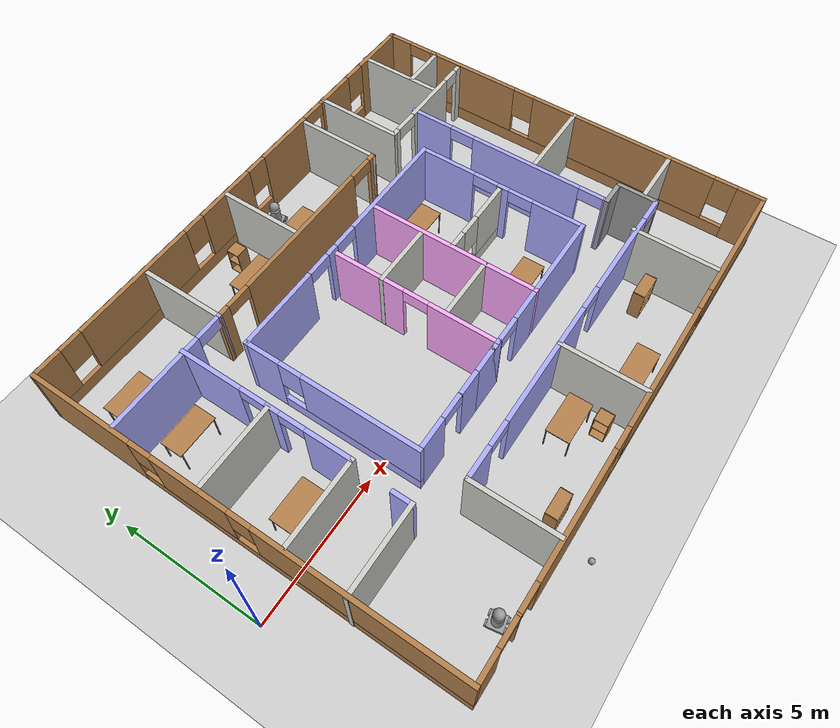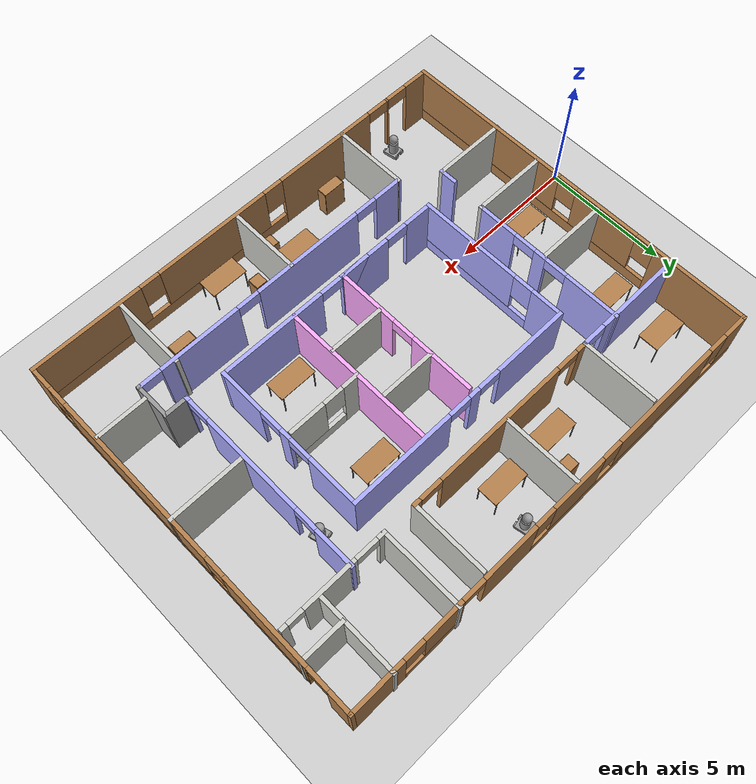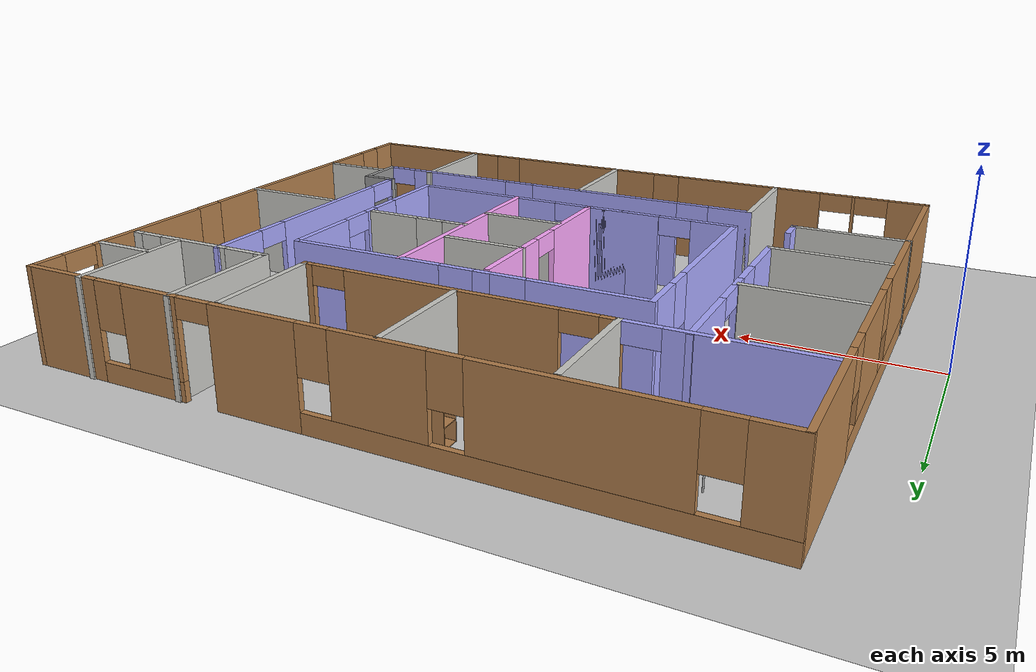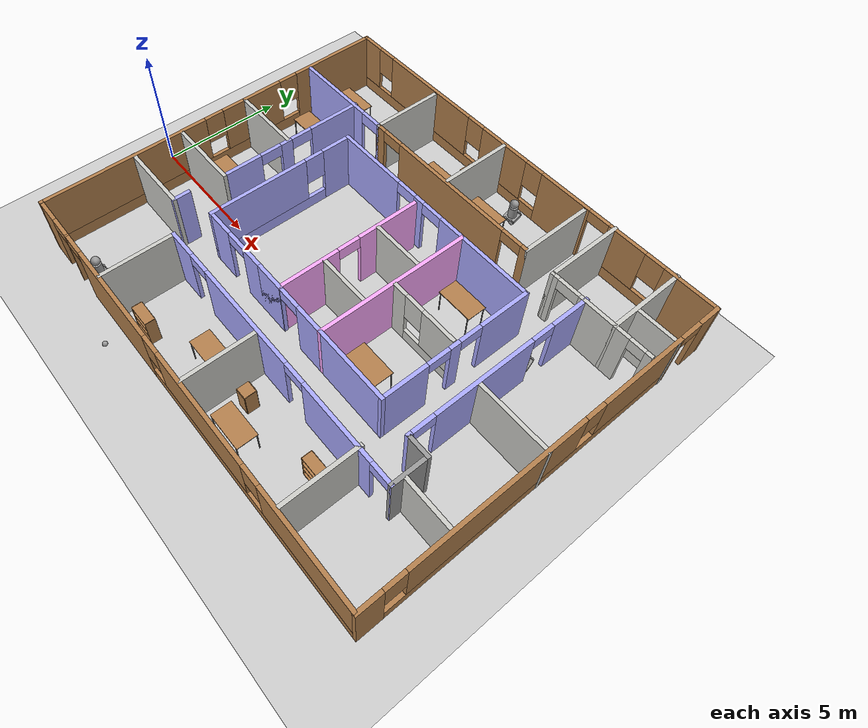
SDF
<sdf version="1.6">
 <world name="default">
  <plugin name="welcome" filename="libwelcome.so"/>
  <light name="sun" type="directional">
   <pose>0 0 10 0 -0 0</pose>
   <diffuse>0.8 0.8 0.8 1</diffuse>
   <specular>0.2 0.2 0.2 1</specular>
   <attenuation>
    <range>1000</range>
    <constant>0.9</constant>
    <linear>0.01</linear>
    <quadratic>0.001</quadratic>
   </attenuation>
   <direction>-0.5 0.1 -0.9</direction>
  </light>
  <model name="ground_plane">
   <static>1</static>
   <link name="link">
    <collision name="collision">
     <geometry><plane><normal>0 0 1</normal><size>100 100</size></plane></geometry>
     <surface>
      <contact><collide_bitmask>65535</collide_bitmask></contact>
      <friction><ode><mu>100</mu><mu2>50</mu2></ode></friction>
     </surface>
    </collision>
    <visual name="visual">
     <cast_shadows>0</cast_shadows>
     <geometry><plane><normal>0 0 1</normal><size>100 100</size></plane></geometry>
     <material>
      <script><uri>file://media/materials/scripts/gazebo.material</uri><name>Gazebo/Grey</name></script>
     </material>
    </visual>
   </link>
  </model>
  <gravity>0 0 -9.8</gravity>
  <magnetic_field>6e-06 2.3e-05 -4.2e-05</magnetic_field>
  <atmosphere type="adiabatic"/>
  <physics name="default_physics" default="0" type="ode">
   <max_step_size>0.001</max_step_size>
   <real_time_factor>1</real_time_factor>
   <real_time_update_rate>1000</real_time_update_rate>
  </physics>
  <scene><ambient>0.4 0.4 0.4 1</ambient><background>0.7 0.7 0.7 1</background><shadows>1</shadows></scene>
  <spherical_coordinates>
   <surface_model>EARTH_WGS84</surface_model>
   <latitude_deg>0</latitude_deg>
   <longitude_deg>0</longitude_deg>
   <elevation>0</elevation>
   <heading_deg>0</heading_deg>
  </spherical_coordinates>
  <model name="newOffice">
   <pose>10.3935 1.72643 0 0 -0 0</pose>
   <link name="Wall_0">
    <pose>-8.92098 -0.018654 0 0 0 -1.5708</pose>
    <visual name="Wall_0_Visual_0">
     <pose>-5.60223 0 1.25 0 -0 0</pose>
     <geometry><box><size>3.79554 0.15 2.5</size></box></geometry>
     <material>
      <script><uri>file://media/materials/scripts/gazebo.material</uri><name>Gazebo/Wood</name></script>
      <ambient>1 0.666667 1 1</ambient>
     </material>
     <meta><layer>0</layer></meta>
    </visual>
    <collision name="Wall_0_Collision_0">
     <geometry><box><size>3.79554 0.15 2.5</size></box></geometry>
     <pose>-5.60223 0 1.25 0 -0 0</pose>
    </collision>
    <visual name="Wall_0_Visual_1">
     <pose>1.89777 0 0.25 0 -0 0</pose>
     <geometry><box><size>11.2045 0.15 0.5</size></box></geometry>
     <material>
      <script><uri>file://media/materials/scripts/gazebo.material</uri><name>Gazebo/Wood</name></script>
      <ambient>1 0.666667 1 1</ambient>
     </material>
     <meta><layer>0</layer></meta>
    </visual>
    <collision name="Wall_0_Collision_1">
     <geometry><box><size>11.2045 0.15 0.5</size></box></geometry>
     <pose>1.89777 0 0.25 0 -0 0</pose>
    </collision>
    <visual name="Wall_0_Visual_2">
     <pose>-1.54552 0 1.5 0 -0 0</pose>
     <geometry><box><size>2.71788 0.15 2</size></box></geometry>
     <material>
      <script><uri>file://media/materials/scripts/gazebo.material</uri><name>Gazebo/Wood</name></script>
      <ambient>1 0.666667 1 1</ambient>
     </material>
     <meta><layer>0</layer></meta>
    </visual>
    <collision name="Wall_0_Collision_2">
     <geometry><box><size>2.71788 0.15 2</size></box></geometry>
     <pose>-1.54552 0 1.5 0 -0 0</pose>
    </collision>
    <visual name="Wall_0_Visual_3">
     <pose>4.05671 0 1.5 0 -0 0</pose>
     <geometry><box><size>6.88658 0.15 2</size></box></geometry>
     <material>
      <script><uri>file://media/materials/scripts/gazebo.material</uri><name>Gazebo/Wood</name></script>
      <ambient>1 0.666667 1 1</ambient>
     </material>
     <meta><layer>0</layer></meta>
    </visual>
    <collision name="Wall_0_Collision_3">
     <geometry><box><size>6.88658 0.15 2</size></box></geometry>
     <pose>4.05671 0 1.5 0 -0 0</pose>
    </collision>
    <visual name="Wall_0_Visual_4">
     <pose>-3.30446 0 1.9 0 -0 0</pose>
     <geometry><box><size>0.8 0.15 1.2</size></box></geometry>
     <material>
      <script><uri>file://media/materials/scripts/gazebo.material</uri><name>Gazebo/Wood</name></script>
      <ambient>1 0.666667 1 1</ambient>
     </material>
     <meta><layer>0</layer></meta>
    </visual>
    <collision name="Wall_0_Collision_4">
     <geometry><box><size>0.8 0.15 1.2</size></box></geometry>
     <pose>-3.30446 0 1.9 0 -0 0</pose>
    </collision>
    <visual name="Wall_0_Visual_5">
     <pose>0.213419 0 1.9 0 -0 0</pose>
     <geometry><box><size>0.8 0.15 1.2</size></box></geometry>
     <material>
      <script><uri>file://media/materials/scripts/gazebo.material</uri><name>Gazebo/Wood</name></script>
      <ambient>1 0.666667 1 1</ambient>
     </material>
     <meta><layer>0</layer></meta>
    </visual>
    <collision name="Wall_0_Collision_5">
     <geometry><box><size>0.8 0.15 1.2</size></box></geometry>
     <pose>0.213419 0 1.9 0 -0 0</pose>
    </collision>
   </link>
   <link name="Wall_1">
    <pose>0.004022 -7.44365 0 0 -0 0</pose>
    <visual name="Wall_1_Visual_0">
     <pose>-8.45097 0 1.25 0 -0 0</pose>
     <geometry><box><size>1.09805 0.15 2.5</size></box></geometry>
     <material>
      <script><uri>file://media/materials/scripts/gazebo.material</uri><name>Gazebo/Wood</name></script>
      <ambient>1 0.666667 1 1</ambient>
     </material>
     <meta><layer>0</layer></meta>
    </visual>
    <collision name="Wall_1_Collision_0">
     <geometry><box><size>1.09805 0.15 2.5</size></box></geometry>
     <pose>-8.45097 0 1.25 0 -0 0</pose>
    </collision>
    <visual name="Wall_1_Visual_1">
     <pose>-6.96251 0 1.25 0 -0 0</pose>
     <geometry><box><size>0.078887 0.15 2.5</size></box></geometry>
     <material>
      <script><uri>file://media/materials/scripts/gazebo.material</uri><name>Gazebo/Wood</name></script>
      <ambient>1 0.666667 1 1</ambient>
     </material>
     <meta><layer>0</layer></meta>
    </visual>
    <collision name="Wall_1_Collision_1">
     <geometry><box><size>0.078887 0.15 2.5</size></box></geometry>
     <pose>-6.96251 0 1.25 0 -0 0</pose>
    </collision>
    <visual name="Wall_1_Visual_2">
     <pose>-3.87848 0 1.25 0 -0 0</pose>
     <geometry><box><size>4.28916 0.15 2.5</size></box></geometry>
     <material>
      <script><uri>file://media/materials/scripts/gazebo.material</uri><name>Gazebo/Wood</name></script>
      <ambient>1 0.666667 1 1</ambient>
     </material>
     <meta><layer>0</layer></meta>
    </visual>
    <collision name="Wall_1_Collision_2">
     <geometry><box><size>4.28916 0.15 2.5</size></box></geometry>
     <pose>-3.87848 0 1.25 0 -0 0</pose>
    </collision>
    <visual name="Wall_1_Visual_3">
     <pose>3.63305 0 0.25 0 -0 0</pose>
     <geometry><box><size>10.7339 0.15 0.5</size></box></geometry>
     <material>
      <script><uri>file://media/materials/scripts/gazebo.material</uri><name>Gazebo/Wood</name></script>
      <ambient>1 0.666667 1 1</ambient>
     </material>
     <meta><layer>0</layer></meta>
    </visual>
    <collision name="Wall_1_Collision_3">
     <geometry><box><size>10.7339 0.15 0.5</size></box></geometry>
     <pose>3.63305 0 0.25 0 -0 0</pose>
    </collision>
    <visual name="Wall_1_Visual_4">
     <pose>1.41922 0 1.5 0 -0 0</pose>
     <geometry><box><size>4.70624 0.15 2</size></box></geometry>
     <material>
      <script><uri>file://media/materials/scripts/gazebo.material</uri><name>Gazebo/Wood</name></script>
      <ambient>1 0.666667 1 1</ambient>
     </material>
     <meta><layer>0</layer></meta>
    </visual>
    <collision name="Wall_1_Collision_4">
     <geometry><box><size>4.70624 0.15 2</size></box></geometry>
     <pose>1.41922 0 1.5 0 -0 0</pose>
    </collision>
    <visual name="Wall_1_Visual_5">
     <pose>6.78617 0 1.5 0 -0 0</pose>
     <geometry><box><size>4.42766 0.15 2</size></box></geometry>
     <material>
      <script><uri>file://media/materials/scripts/gazebo.material</uri><name>Gazebo/Wood</name></script>
      <ambient>1 0.666667 1 1</ambient>
     </material>
     <meta><layer>0</layer></meta>
    </visual>
    <collision name="Wall_1_Collision_5">
     <geometry><box><size>4.42766 0.15 2</size></box></geometry>
     <pose>6.78617 0 1.5 0 -0 0</pose>
    </collision>
    <visual name="Wall_1_Visual_6">
     <pose>-1.3339 0 1.9 0 -0 0</pose>
     <geometry><box><size>0.8 0.15 1.2</size></box></geometry>
     <material>
      <script><uri>file://media/materials/scripts/gazebo.material</uri><name>Gazebo/Wood</name></script>
      <ambient>1 0.666667 1 1</ambient>
     </material>
     <meta><layer>0</layer></meta>
    </visual>
    <collision name="Wall_1_Collision_6">
     <geometry><box><size>0.8 0.15 1.2</size></box></geometry>
     <pose>-1.3339 0 1.9 0 -0 0</pose>
    </collision>
    <visual name="Wall_1_Visual_7">
     <pose>4.17234 0 1.9 0 -0 0</pose>
     <geometry><box><size>0.8 0.15 1.2</size></box></geometry>
     <material>
      <script><uri>file://media/materials/scripts/gazebo.material</uri><name>Gazebo/Wood</name></script>
      <ambient>1 0.666667 1 1</ambient>
     </material>
     <meta><layer>0</layer></meta>
    </visual>
    <collision name="Wall_1_Collision_7">
     <geometry><box><size>0.8 0.15 1.2</size></box></geometry>
     <pose>4.17234 0 1.9 0 -0 0</pose>
    </collision>
    <visual name="Wall_1_Visual_8">
     <pose>-7.45195 0 2.25 0 -0 0</pose>
     <geometry><box><size>0.9 0.15 0.5</size></box></geometry>
     <material>
      <script><uri>file://media/materials/scripts/gazebo.material</uri><name>Gazebo/Wood</name></script>
      <ambient>1 0.666667 1 1</ambient>
     </material>
     <meta><layer>0</layer></meta>
    </visual>
    <collision name="Wall_1_Collision_8">
     <geometry><box><size>0.9 0.15 0.5</size></box></geometry>
     <pose>-7.45195 0 2.25 0 -0 0</pose>
    </collision>
    <visual name="Wall_1_Visual_9">
     <pose>-6.47306 0 2.25 0 -0 0</pose>
     <geometry><box><size>0.9 0.15 0.5</size></box></geometry>
     <material>
      <script><uri>file://media/materials/scripts/gazebo.material</uri><name>Gazebo/Wood</name></script>
      <ambient>1 0.666667 1 1</ambient>
     </material>
     <meta><layer>0</layer></meta>
    </visual>
    <collision name="Wall_1_Collision_9">
     <geometry><box><size>0.9 0.15 0.5</size></box></geometry>
     <pose>-6.47306 0 2.25 0 -0 0</pose>
    </collision>
   </link>
   <link name="Wall_11">
    <collision name="Wall_11_Collision">
     <geometry><box><size>3 0.15 2.5</size></box></geometry>
     <pose>0 0 1.25 0 -0 0</pose>
    </collision>
    <visual name="Wall_11_Visual">
     <pose>0 0 1.25 0 -0 0</pose>
     <geometry><box><size>3 0.15 2.5</size></box></geometry>
     <material>
      <script><uri>file://media/materials/scripts/gazebo.material</uri><name>Gazebo/CeilingTiled</name></script>
      <ambient>0.760784 0.662745 0.627451 1</ambient>
     </material>
     <meta><layer>0</layer></meta>
    </visual>
    <pose>-0.660428 5.89112 0 0 -0 1.5708</pose>
   </link>
   <link name="Wall_13">
    <collision name="Wall_13_Collision">
     <geometry><box><size>3.25 0.15 2.5</size></box></geometry>
     <pose>0 0 1.25 0 -0 0</pose>
    </collision>
    <visual name="Wall_13_Visual">
     <pose>0 0 1.25 0 -0 0</pose>
     <geometry><box><size>3.25 0.15 2.5</size></box></geometry>
     <material>
      <script><uri>file://media/materials/scripts/gazebo.material</uri><name>Gazebo/CeilingTiled</name></script>
      <ambient>0.760784 0.662745 0.627451 1</ambient>
     </material>
     <meta><layer>0</layer></meta>
    </visual>
    <pose>4.6433 5.89365 0 0 0 -1.5708</pose>
   </link>
   <link name="Wall_14">
    <pose>6.6933 4.34365 0 0 -0 0</pose>
    <visual name="Wall_14_Visual_0">
     <pose>-1.94946 0 1.25 0 -0 0</pose>
     <geometry><box><size>0.351082 0.15 2.5</size></box></geometry>
     <material>
      <script><uri>file://media/materials/scripts/gazebo.material</uri><name>Gazebo/CeilingTiled</name></script>
      <ambient>0.760784 0.662745 0.627451 1</ambient>
     </material>
     <meta><layer>0</layer></meta>
    </visual>
    <collision name="Wall_14_Collision_0">
     <geometry><box><size>0.351082 0.15 2.5</size></box></geometry>
     <pose>-1.94946 0 1.25 0 -0 0</pose>
    </collision>
    <visual name="Wall_14_Visual_1">
     <pose>0.175003 0 1.25 0 -0 0</pose>
     <geometry><box><size>2.09784 0.15 2.5</size></box></geometry>
     <material>
      <script><uri>file://media/materials/scripts/gazebo.material</uri><name>Gazebo/CeilingTiled</name></script>
      <ambient>0.760784 0.662745 0.627451 1</ambient>
     </material>
     <meta><layer>0</layer></meta>
    </visual>
    <collision name="Wall_14_Collision_1">
     <geometry><box><size>2.09784 0.15 2.5</size></box></geometry>
     <pose>0.175003 0 1.25 0 -0 0</pose>
    </collision>
    <visual name="Wall_14_Visual_2">
     <pose>1.98681 0 1.25 0 -0 0</pose>
     <geometry><box><size>0.276388 0.15 2.5</size></box></geometry>
     <material>
      <script><uri>file://media/materials/scripts/gazebo.material</uri><name>Gazebo/CeilingTiled</name></script>
      <ambient>0.760784 0.662745 0.627451 1</ambient>
     </material>
     <meta><layer>0</layer></meta>
    </visual>
    <collision name="Wall_14_Collision_2">
     <geometry><box><size>0.276388 0.15 2.5</size></box></geometry>
     <pose>1.98681 0 1.25 0 -0 0</pose>
    </collision>
    <visual name="Wall_14_Visual_3">
     <pose>-1.32392 0 2.25 0 -0 0</pose>
     <geometry><box><size>0.9 0.15 0.5</size></box></geometry>
     <material>
      <script><uri>file://media/materials/scripts/gazebo.material</uri><name>Gazebo/CeilingTiled</name></script>
      <ambient>0.760784 0.662745 0.627451 1</ambient>
     </material>
     <meta><layer>0</layer></meta>
    </visual>
    <collision name="Wall_14_Collision_3">
     <geometry><box><size>0.9 0.15 0.5</size></box></geometry>
     <pose>-1.32392 0 2.25 0 -0 0</pose>
    </collision>
    <visual name="Wall_14_Visual_4">
     <pose>1.53627 0 2.25 0 -0 0</pose>
     <geometry><box><size>0.624688 0.15 0.5</size></box></geometry>
     <material>
      <script><uri>file://media/materials/scripts/gazebo.material</uri><name>Gazebo/CeilingTiled</name></script>
      <ambient>0.760784 0.662745 0.627451 1</ambient>
     </material>
     <meta><layer>0</layer></meta>
    </visual>
    <collision name="Wall_14_Collision_4">
     <geometry><box><size>0.624688 0.15 0.5</size></box></geometry>
     <pose>1.53627 0 2.25 0 -0 0</pose>
    </collision>
   </link>
   <link name="Wall_16">
    <collision name="Wall_16_Collision">
     <geometry><box><size>3.25 0.15 2.5</size></box></geometry>
     <pose>0 0 1.25 0 -0 0</pose>
    </collision>
    <visual name="Wall_16_Visual">
     <pose>0 0 1.25 0 -0 0</pose>
     <geometry><box><size>3.25 0.15 2.5</size></box></geometry>
     <material>
      <script><uri>file://media/materials/scripts/gazebo.material</uri><name>Gazebo/CeilingTiled</name></script>
      <ambient>0.760784 0.662745 0.627451 1</ambient>
     </material>
     <meta><layer>0</layer></meta>
    </visual>
    <pose>7.29516 5.89365 0 0 0 -1.5708</pose>
   </link>
   <link name="Wall_18">
    <collision name="Wall_18_Collision">
     <geometry><box><size>1.75 0.15 2.5</size></box></geometry>
     <pose>0 0 1.25 0 -0 0</pose>
    </collision>
    <visual name="Wall_18_Visual">
     <pose>0 0 1.25 0 -0 0</pose>
     <geometry><box><size>1.75 0.15 2.5</size></box></geometry>
     <material>
      <script><uri>file://media/materials/scripts/gazebo.material</uri><name>Gazebo/CeilingTiled</name></script>
      <ambient>0.760784 0.662745 0.627451 1</ambient>
     </material>
     <meta><layer>0</layer></meta>
    </visual>
    <pose>8.14169 5.3966 0 0 -0 0</pose>
   </link>
   <link name="Wall_2">
    <pose>8.92902 -0.018654 0 0 -0 1.5708</pose>
    <visual name="Wall_2_Visual_0">
     <pose>-7.00867 0 1.25 0 -0 0</pose>
     <geometry><box><size>0.982667 0.15 2.5</size></box></geometry>
     <material>
      <script><uri>file://media/materials/scripts/gazebo.material</uri><name>Gazebo/Wood</name></script>
      <ambient>1 0.666667 1 1</ambient>
     </material>
     <meta><layer>0</layer></meta>
    </visual>
    <collision name="Wall_2_Collision_0">
     <geometry><box><size>0.982667 0.15 2.5</size></box></geometry>
     <pose>-7.00867 0 1.25 0 -0 0</pose>
    </collision>
    <visual name="Wall_2_Visual_1">
     <pose>7.01908 0 1.25 0 -0 0</pose>
     <geometry><box><size>0.961832 0.15 2.5</size></box></geometry>
     <material>
      <script><uri>file://media/materials/scripts/gazebo.material</uri><name>Gazebo/Wood</name></script>
      <ambient>1 0.666667 1 1</ambient>
     </material>
     <meta><layer>0</layer></meta>
    </visual>
    <collision name="Wall_2_Collision_1">
     <geometry><box><size>0.961832 0.15 2.5</size></box></geometry>
     <pose>7.01908 0 1.25 0 -0 0</pose>
    </collision>
    <visual name="Wall_2_Visual_2">
     <pose>-0.439582 0 0.25 0 -0 0</pose>
     <geometry><box><size>12.1555 0.15 0.5</size></box></geometry>
     <material>
      <script><uri>file://media/materials/scripts/gazebo.material</uri><name>Gazebo/Wood</name></script>
      <ambient>1 0.666667 1 1</ambient>
     </material>
     <meta><layer>0</layer></meta>
    </visual>
    <collision name="Wall_2_Collision_2">
     <geometry><box><size>12.1555 0.15 0.5</size></box></geometry>
     <pose>-0.439582 0 0.25 0 -0 0</pose>
    </collision>
    <visual name="Wall_2_Visual_3">
     <pose>-2.24767 0 1.5 0 -0 0</pose>
     <geometry><box><size>6.93933 0.15 2</size></box></geometry>
     <material>
      <script><uri>file://media/materials/scripts/gazebo.material</uri><name>Gazebo/Wood</name></script>
      <ambient>1 0.666667 1 1</ambient>
     </material>
     <meta><layer>0</layer></meta>
    </visual>
    <collision name="Wall_2_Collision_3">
     <geometry><box><size>6.93933 0.15 2</size></box></geometry>
     <pose>-2.24767 0 1.5 0 -0 0</pose>
    </collision>
    <visual name="Wall_2_Visual_4">
     <pose>3.83008 0 1.5 0 -0 0</pose>
     <geometry><box><size>3.61617 0.15 2</size></box></geometry>
     <material>
      <script><uri>file://media/materials/scripts/gazebo.material</uri><name>Gazebo/Wood</name></script>
      <ambient>1 0.666667 1 1</ambient>
     </material>
     <meta><layer>0</layer></meta>
    </visual>
    <collision name="Wall_2_Collision_4">
     <geometry><box><size>3.61617 0.15 2</size></box></geometry>
     <pose>3.83008 0 1.5 0 -0 0</pose>
    </collision>
    <visual name="Wall_2_Visual_5">
     <pose>-6.11733 0 1.9 0 -0 0</pose>
     <geometry><box><size>0.8 0.15 1.2</size></box></geometry>
     <material>
      <script><uri>file://media/materials/scripts/gazebo.material</uri><name>Gazebo/Wood</name></script>
      <ambient>1 0.666667 1 1</ambient>
     </material>
     <meta><layer>0</layer></meta>
    </visual>
    <collision name="Wall_2_Collision_5">
     <geometry><box><size>0.8 0.15 1.2</size></box></geometry>
     <pose>-6.11733 0 1.9 0 -0 0</pose>
    </collision>
    <visual name="Wall_2_Visual_6">
     <pose>1.622 0 1.9 0 -0 0</pose>
     <geometry><box><size>0.8 0.15 1.2</size></box></geometry>
     <material>
      <script><uri>file://media/materials/scripts/gazebo.material</uri><name>Gazebo/Wood</name></script>
      <ambient>1 0.666667 1 1</ambient>
     </material>
     <meta><layer>0</layer></meta>
    </visual>
    <collision name="Wall_2_Collision_6">
     <geometry><box><size>0.8 0.15 1.2</size></box></geometry>
     <pose>1.622 0 1.9 0 -0 0</pose>
    </collision>
    <visual name="Wall_2_Visual_7">
     <pose>6.08817 0 2.25 0 -0 0</pose>
     <geometry><box><size>0.9 0.15 0.5</size></box></geometry>
     <material>
      <script><uri>file://media/materials/scripts/gazebo.material</uri><name>Gazebo/Wood</name></script>
      <ambient>1 0.666667 1 1</ambient>
     </material>
     <meta><layer>0</layer></meta>
    </visual>
    <collision name="Wall_2_Collision_7">
     <geometry><box><size>0.9 0.15 0.5</size></box></geometry>
     <pose>6.08817 0 2.25 0 -0 0</pose>
    </collision>
   </link>
   <link name="Wall_20">
    <pose>-5.96415 1.3696 0 0 0 -1.5708</pose>
    <visual name="Wall_20_Visual_0">
     <pose>-1.99614 0 1.25 0 -0 0</pose>
     <geometry><box><size>2.25772 0.15 2.5</size></box></geometry>
     <material>
      <script><uri>file://media/materials/scripts/gazebo.material</uri><name>Gazebo/Grey</name></script>
      <ambient>0.666667 0.666667 1 1</ambient>
     </material>
     <meta><layer>0</layer></meta>
    </visual>
    <collision name="Wall_20_Collision_0">
     <geometry><box><size>2.25772 0.15 2.5</size></box></geometry>
     <pose>-1.99614 0 1.25 0 -0 0</pose>
    </collision>
    <visual name="Wall_20_Visual_1">
     <pose>0.286292 0 1.25 0 -0 0</pose>
     <geometry><box><size>0.507151 0.15 2.5</size></box></geometry>
     <material>
      <script><uri>file://media/materials/scripts/gazebo.material</uri><name>Gazebo/Grey</name></script>
      <ambient>0.666667 0.666667 1 1</ambient>
     </material>
     <meta><layer>0</layer></meta>
    </visual>
    <collision name="Wall_20_Collision_1">
     <geometry><box><size>0.507151 0.15 2.5</size></box></geometry>
     <pose>0.286292 0 1.25 0 -0 0</pose>
    </collision>
    <visual name="Wall_20_Visual_2">
     <pose>2.28243 0 1.25 0 -0 0</pose>
     <geometry><box><size>1.68513 0.15 2.5</size></box></geometry>
     <material>
      <script><uri>file://media/materials/scripts/gazebo.material</uri><name>Gazebo/Grey</name></script>
      <ambient>0.666667 0.666667 1 1</ambient>
     </material>
     <meta><layer>0</layer></meta>
    </visual>
    <collision name="Wall_20_Collision_2">
     <geometry><box><size>1.68513 0.15 2.5</size></box></geometry>
     <pose>2.28243 0 1.25 0 -0 0</pose>
    </collision>
    <visual name="Wall_20_Visual_3">
     <pose>-0.417283 0 2.25 0 -0 0</pose>
     <geometry><box><size>0.9 0.15 0.5</size></box></geometry>
     <material>
      <script><uri>file://media/materials/scripts/gazebo.material</uri><name>Gazebo/Grey</name></script>
      <ambient>0.666667 0.666667 1 1</ambient>
     </material>
     <meta><layer>0</layer></meta>
    </visual>
    <collision name="Wall_20_Collision_3">
     <geometry><box><size>0.9 0.15 0.5</size></box></geometry>
     <pose>-0.417283 0 2.25 0 -0 0</pose>
    </collision>
    <visual name="Wall_20_Visual_4">
     <pose>0.989867 0 2.25 0 -0 0</pose>
     <geometry><box><size>0.9 0.15 0.5</size></box></geometry>
     <material>
      <script><uri>file://media/materials/scripts/gazebo.material</uri><name>Gazebo/Grey</name></script>
      <ambient>0.666667 0.666667 1 1</ambient>
     </material>
     <meta><layer>0</layer></meta>
    </visual>
    <collision name="Wall_20_Collision_4">
     <geometry><box><size>0.9 0.15 0.5</size></box></geometry>
     <pose>0.989867 0 2.25 0 -0 0</pose>
    </collision>
   </link>
   <link name="Wall_21">
    <collision name="Wall_21_Collision">
     <geometry><box><size>3 0.15 2.5</size></box></geometry>
     <pose>0 0 1.25 0 -0 0</pose>
    </collision>
    <visual name="Wall_21_Visual">
     <pose>0 0 1.25 0 -0 0</pose>
     <geometry><box><size>3 0.15 2.5</size></box></geometry>
     <material>
      <script><uri>file://media/materials/scripts/gazebo.material</uri><name>Gazebo/CeilingTiled</name></script>
      <ambient>0.760784 0.662745 0.627451 1</ambient>
     </material>
     <meta><layer>0</layer></meta>
    </visual>
    <pose>-7.38915 -1.6804 0 0 -0 3.14159</pose>
   </link>
   <link name="Wall_23">
    <collision name="Wall_23_Collision">
     <geometry><box><size>3 0.15 2.5</size></box></geometry>
     <pose>0 0 1.25 0 -0 0</pose>
    </collision>
    <visual name="Wall_23_Visual">
     <pose>0 0 1.25 0 -0 0</pose>
     <geometry><box><size>3 0.15 2.5</size></box></geometry>
     <material>
      <script><uri>file://media/materials/scripts/gazebo.material</uri><name>Gazebo/CeilingTiled</name></script>
      <ambient>0.760784 0.662745 0.627451 1</ambient>
     </material>
     <meta><layer>0</layer></meta>
    </visual>
    <pose>-7.47016 1.20945 0 0 -0 0</pose>
   </link>
   <link name="Wall_25">
    <collision name="Wall_25_Collision">
     <geometry><box><size>3 0.15 2.5</size></box></geometry>
     <pose>0 0 1.25 0 -0 0</pose>
    </collision>
    <visual name="Wall_25_Visual">
     <pose>0 0 1.25 0 -0 0</pose>
     <geometry><box><size>3 0.15 2.5</size></box></geometry>
     <material>
      <script><uri>file://media/materials/scripts/gazebo.material</uri><name>Gazebo/CeilingTiled</name></script>
      <ambient>0.760784 0.662745 0.627451 1</ambient>
     </material>
     <meta><layer>0</layer></meta>
    </visual>
    <pose>-7.51668 -3.72208 0 0 -0 0</pose>
   </link>
   <link name="Wall_26">
    <collision name="Wall_26_Collision">
     <geometry><box><size>0.75 0.15 2.5</size></box></geometry>
     <pose>0 0 1.25 0 -0 0</pose>
    </collision>
    <visual name="Wall_26_Visual">
     <pose>0 0 1.25 0 -0 0</pose>
     <geometry><box><size>0.75 0.15 2.5</size></box></geometry>
     <material>
      <script><uri>file://media/materials/scripts/gazebo.material</uri><name>Gazebo/Grey</name></script>
      <ambient>0.666667 0.666667 1 1</ambient>
     </material>
     <meta><layer>0</layer></meta>
    </visual>
    <pose>-6.09169 -3.42209 0 0 -0 1.5708</pose>
   </link>
   <link name="Wall_28">
    <pose>-4.70801 0.020406 0 0 0 -1.5708</pose>
    <visual name="Wall_28_Visual_0">
     <pose>-2.47749 0 1.25 0 -0 0</pose>
     <geometry><box><size>1.29502 0.15 2.5</size></box></geometry>
     <material>
      <script><uri>file://media/materials/scripts/gazebo.material</uri><name>Gazebo/Grey</name></script>
      <ambient>0.666667 0.666667 1 1</ambient>
     </material>
     <meta><layer>0</layer></meta>
    </visual>
    <collision name="Wall_28_Collision_0">
     <geometry><box><size>1.29502 0.15 2.5</size></box></geometry>
     <pose>-2.47749 0 1.25 0 -0 0</pose>
    </collision>
    <visual name="Wall_28_Visual_1">
     <pose>0.647508 0 0.25 0 -0 0</pose>
     <geometry><box><size>4.95498 0.15 0.5</size></box></geometry>
     <material>
      <script><uri>file://media/materials/scripts/gazebo.material</uri><name>Gazebo/Grey</name></script>
      <ambient>0.666667 0.666667 1 1</ambient>
     </material>
     <meta><layer>0</layer></meta>
    </visual>
    <collision name="Wall_28_Collision_1">
     <geometry><box><size>4.95498 0.15 0.5</size></box></geometry>
     <pose>0.647508 0 0.25 0 -0 0</pose>
    </collision>
    <visual name="Wall_28_Visual_2">
     <pose>1.04751 0 1.5 0 -0 0</pose>
     <geometry><box><size>4.15498 0.15 2</size></box></geometry>
     <material>
      <script><uri>file://media/materials/scripts/gazebo.material</uri><name>Gazebo/Grey</name></script>
      <ambient>0.666667 0.666667 1 1</ambient>
     </material>
     <meta><layer>0</layer></meta>
    </visual>
    <collision name="Wall_28_Collision_2">
     <geometry><box><size>4.15498 0.15 2</size></box></geometry>
     <pose>1.04751 0 1.5 0 -0 0</pose>
    </collision>
    <visual name="Wall_28_Visual_3">
     <pose>-1.42998 0 1.9 0 -0 0</pose>
     <geometry><box><size>0.8 0.15 1.2</size></box></geometry>
     <material>
      <script><uri>file://media/materials/scripts/gazebo.material</uri><name>Gazebo/Grey</name></script>
      <ambient>0.666667 0.666667 1 1</ambient>
     </material>
     <meta><layer>0</layer></meta>
    </visual>
    <collision name="Wall_28_Collision_3">
     <geometry><box><size>0.8 0.15 1.2</size></box></geometry>
     <pose>-1.42998 0 1.9 0 -0 0</pose>
    </collision>
   </link>
   <link name="Wall_29">
    <pose>-2.65801 -3.02959 0 0 -0 0</pose>
    <visual name="Wall_29_Visual_0">
     <pose>-1.51055 0 1.25 0 -0 0</pose>
     <geometry><box><size>1.2289 0.15 2.5</size></box></geometry>
     <material>
      <script><uri>file://media/materials/scripts/gazebo.material</uri><name>Gazebo/Grey</name></script>
      <ambient>0.666667 0.666667 1 1</ambient>
     </material>
     <meta><layer>0</layer></meta>
    </visual>
    <collision name="Wall_29_Collision_0">
     <geometry><box><size>1.2289 0.15 2.5</size></box></geometry>
     <pose>-1.51055 0 1.25 0 -0 0</pose>
    </collision>
    <visual name="Wall_29_Visual_1">
     <pose>1.06445 0 1.25 0 -0 0</pose>
     <geometry><box><size>2.1211 0.15 2.5</size></box></geometry>
     <material>
      <script><uri>file://media/materials/scripts/gazebo.material</uri><name>Gazebo/Grey</name></script>
      <ambient>0.666667 0.666667 1 1</ambient>
     </material>
     <meta><layer>0</layer></meta>
    </visual>
    <collision name="Wall_29_Collision_1">
     <geometry><box><size>2.1211 0.15 2.5</size></box></geometry>
     <pose>1.06445 0 1.25 0 -0 0</pose>
    </collision>
    <visual name="Wall_29_Visual_2">
     <pose>1.50801 0 1.25 0 -0 0</pose>
     <geometry><box><size>1.23399 0.15 2.5</size></box></geometry>
     <material>
      <script><uri>file://media/materials/scripts/gazebo.material</uri><name>Gazebo/Grey</name></script>
      <ambient>0.666667 0.666667 1 1</ambient>
     </material>
     <meta><layer>0</layer></meta>
    </visual>
    <collision name="Wall_29_Collision_2">
     <geometry><box><size>1.23399 0.15 2.5</size></box></geometry>
     <pose>1.50801 0 1.25 0 -0 0</pose>
    </collision>
    <visual name="Wall_29_Visual_3">
     <pose>-0.452546 0 2.25 0 -0 0</pose>
     <geometry><box><size>0.887117 0.15 0.5</size></box></geometry>
     <material>
      <script><uri>file://media/materials/scripts/gazebo.material</uri><name>Gazebo/Grey</name></script>
      <ambient>0.666667 0.666667 1 1</ambient>
     </material>
     <meta><layer>0</layer></meta>
    </visual>
    <collision name="Wall_29_Collision_3">
     <geometry><box><size>0.887117 0.15 0.5</size></box></geometry>
     <pose>-0.452546 0 2.25 0 -0 0</pose>
    </collision>
   </link>
   <link name="Wall_3">
    <pose>0.004022 7.40635 0 0 -0 3.14159</pose>
    <visual name="Wall_3_Visual_0">
     <pose>-7.91801 0 1.25 0 -0 0</pose>
     <geometry><box><size>2.16398 0.15 2.5</size></box></geometry>
     <material>
      <script><uri>file://media/materials/scripts/gazebo.material</uri><name>Gazebo/Wood</name></script>
      <ambient>1 0.666667 1 1</ambient>
     </material>
     <meta><layer>0</layer></meta>
    </visual>
    <collision name="Wall_3_Collision_0">
     <geometry><box><size>2.16398 0.15 2.5</size></box></geometry>
     <pose>-7.91801 0 1.25 0 -0 0</pose>
    </collision>
    <visual name="Wall_3_Visual_1">
     <pose>-2.4037 0 1.25 0 -0 0</pose>
     <geometry><box><size>2.2702 0.15 2.5</size></box></geometry>
     <material>
      <script><uri>file://media/materials/scripts/gazebo.material</uri><name>Gazebo/Wood</name></script>
      <ambient>1 0.666667 1 1</ambient>
     </material>
     <meta><layer>0</layer></meta>
    </visual>
    <collision name="Wall_3_Collision_1">
     <geometry><box><size>2.2702 0.15 2.5</size></box></geometry>
     <pose>-2.4037 0 1.25 0 -0 0</pose>
    </collision>
    <visual name="Wall_3_Visual_2">
     <pose>-5.63741 0 0.25 0 -0 0</pose>
     <geometry><box><size>2.39722 0.15 0.5</size></box></geometry>
     <material>
      <script><uri>file://media/materials/scripts/gazebo.material</uri><name>Gazebo/Wood</name></script>
      <ambient>1 0.666667 1 1</ambient>
     </material>
     <meta><layer>0</layer></meta>
    </visual>
    <collision name="Wall_3_Collision_2">
     <geometry><box><size>2.39722 0.15 0.5</size></box></geometry>
     <pose>-5.63741 0 0.25 0 -0 0</pose>
    </collision>
    <visual name="Wall_3_Visual_3">
     <pose>3.8657 0 0.25 0 -0 0</pose>
     <geometry><box><size>10.2686 0.15 0.5</size></box></geometry>
     <material>
      <script><uri>file://media/materials/scripts/gazebo.material</uri><name>Gazebo/Wood</name></script>
      <ambient>1 0.666667 1 1</ambient>
     </material>
     <meta><layer>0</layer></meta>
    </visual>
    <collision name="Wall_3_Collision_3">
     <geometry><box><size>10.2686 0.15 0.5</size></box></geometry>
     <pose>3.8657 0 0.25 0 -0 0</pose>
    </collision>
    <visual name="Wall_3_Visual_4">
     <pose>-5.23741 0 1.5 0 -0 0</pose>
     <geometry><box><size>1.59722 0.15 2</size></box></geometry>
     <material>
      <script><uri>file://media/materials/scripts/gazebo.material</uri><name>Gazebo/Wood</name></script>
      <ambient>1 0.666667 1 1</ambient>
     </material>
     <meta><layer>0</layer></meta>
    </visual>
    <collision name="Wall_3_Collision_4">
     <geometry><box><size>1.59722 0.15 2</size></box></geometry>
     <pose>-5.23741 0 1.5 0 -0 0</pose>
    </collision>
    <visual name="Wall_3_Visual_5">
     <pose>-5.23741 0 1.5 0 -0 0</pose>
     <geometry><box><size>1.59722 0.15 2</size></box></geometry>
     <material>
      <script><uri>file://media/materials/scripts/gazebo.material</uri><name>Gazebo/Wood</name></script>
      <ambient>1 0.666667 1 1</ambient>
     </material>
     <meta><layer>0</layer></meta>
    </visual>
    <collision name="Wall_3_Collision_5">
     <geometry><box><size>1.59722 0.15 2</size></box></geometry>
     <pose>-5.23741 0 1.5 0 -0 0</pose>
    </collision>
    <visual name="Wall_3_Visual_6">
     <pose>0.676212 0 1.5 0 -0 0</pose>
     <geometry><box><size>2.28961 0.15 2</size></box></geometry>
     <material>
      <script><uri>file://media/materials/scripts/gazebo.material</uri><name>Gazebo/Wood</name></script>
      <ambient>1 0.666667 1 1</ambient>
     </material>
     <meta><layer>0</layer></meta>
    </visual>
    <collision name="Wall_3_Collision_6">
     <geometry><box><size>2.28961 0.15 2</size></box></geometry>
     <pose>0.676212 0 1.5 0 -0 0</pose>
    </collision>
    <visual name="Wall_3_Visual_7">
     <pose>4.88237 0 1.5 0 -0 0</pose>
     <geometry><box><size>4.5227 0.15 2</size></box></geometry>
     <material>
      <script><uri>file://media/materials/scripts/gazebo.material</uri><name>Gazebo/Wood</name></script>
      <ambient>1 0.666667 1 1</ambient>
     </material>
     <meta><layer>0</layer></meta>
    </visual>
    <collision name="Wall_3_Collision_7">
     <geometry><box><size>4.5227 0.15 2</size></box></geometry>
     <pose>4.88237 0 1.5 0 -0 0</pose>
    </collision>
    <visual name="Wall_3_Visual_8">
     <pose>8.47186 0 1.5 0 -0 0</pose>
     <geometry><box><size>1.05628 0.15 2</size></box></geometry>
     <material>
      <script><uri>file://media/materials/scripts/gazebo.material</uri><name>Gazebo/Wood</name></script>
      <ambient>1 0.666667 1 1</ambient>
     </material>
     <meta><layer>0</layer></meta>
    </visual>
    <collision name="Wall_3_Collision_8">
     <geometry><box><size>1.05628 0.15 2</size></box></geometry>
     <pose>8.47186 0 1.5 0 -0 0</pose>
    </collision>
    <visual name="Wall_3_Visual_9">
     <pose>-6.43602 0 1.9 0 -0 0</pose>
     <geometry><box><size>0.8 0.15 1.2</size></box></geometry>
     <material>
      <script><uri>file://media/materials/scripts/gazebo.material</uri><name>Gazebo/Wood</name></script>
      <ambient>1 0.666667 1 1</ambient>
     </material>
     <meta><layer>0</layer></meta>
    </visual>
    <collision name="Wall_3_Collision_9">
     <geometry><box><size>0.8 0.15 1.2</size></box></geometry>
     <pose>-6.43602 0 1.9 0 -0 0</pose>
    </collision>
    <visual name="Wall_3_Visual_10">
     <pose>-0.868594 0 1.9 0 -0 0</pose>
     <geometry><box><size>0.8 0.15 1.2</size></box></geometry>
     <material>
      <script><uri>file://media/materials/scripts/gazebo.material</uri><name>Gazebo/Wood</name></script>
      <ambient>1 0.666667 1 1</ambient>
     </material>
     <meta><layer>0</layer></meta>
    </visual>
    <collision name="Wall_3_Collision_10">
     <geometry><box><size>0.8 0.15 1.2</size></box></geometry>
     <pose>-0.868594 0 1.9 0 -0 0</pose>
    </collision>
    <visual name="Wall_3_Visual_11">
     <pose>2.22102 0 1.9 0 -0 0</pose>
     <geometry><box><size>0.8 0.15 1.2</size></box></geometry>
     <material>
      <script><uri>file://media/materials/scripts/gazebo.material</uri><name>Gazebo/Wood</name></script>
      <ambient>1 0.666667 1 1</ambient>
     </material>
     <meta><layer>0</layer></meta>
    </visual>
    <collision name="Wall_3_Collision_11">
     <geometry><box><size>0.8 0.15 1.2</size></box></geometry>
     <pose>2.22102 0 1.9 0 -0 0</pose>
    </collision>
    <visual name="Wall_3_Visual_12">
     <pose>7.54372 0 1.9 0 -0 0</pose>
     <geometry><box><size>0.8 0.15 1.2</size></box></geometry>
     <material>
      <script><uri>file://media/materials/scripts/gazebo.material</uri><name>Gazebo/Wood</name></script>
      <ambient>1 0.666667 1 1</ambient>
     </material>
     <meta><layer>0</layer></meta>
    </visual>
    <collision name="Wall_3_Collision_12">
     <geometry><box><size>0.8 0.15 1.2</size></box></geometry>
     <pose>7.54372 0 1.9 0 -0 0</pose>
    </collision>
    <visual name="Wall_3_Visual_13">
     <pose>-3.9888 0 2.25 0 -0 0</pose>
     <geometry><box><size>0.9 0.15 0.5</size></box></geometry>
     <material>
      <script><uri>file://media/materials/scripts/gazebo.material</uri><name>Gazebo/Wood</name></script>
      <ambient>1 0.666667 1 1</ambient>
     </material>
     <meta><layer>0</layer></meta>
    </visual>
    <collision name="Wall_3_Collision_13">
     <geometry><box><size>0.9 0.15 0.5</size></box></geometry>
     <pose>-3.9888 0 2.25 0 -0 0</pose>
    </collision>
    <visual name="Wall_3_Visual_14">
     <pose>-3.9888 0 2.25 0 -0 0</pose>
     <geometry><box><size>0.9 0.15 0.5</size></box></geometry>
     <material>
      <script><uri>file://media/materials/scripts/gazebo.material</uri><name>Gazebo/Wood</name></script>
      <ambient>1 0.666667 1 1</ambient>
     </material>
     <meta><layer>0</layer></meta>
    </visual>
    <collision name="Wall_3_Collision_14">
     <geometry><box><size>0.9 0.15 0.5</size></box></geometry>
     <pose>-3.9888 0 2.25 0 -0 0</pose>
    </collision>
   </link>
   <link name="Wall_30">
    <pose>-0.60801 -0.104594 0 0 -0 1.5708</pose>
    <visual name="Wall_30_Visual_0">
     <pose>-1.74285 0 1.25 0 -0 0</pose>
     <geometry><box><size>2.51429 0.15 2.5</size></box></geometry>
     <material>
      <script><uri>file://media/materials/scripts/gazebo.material</uri><name>Gazebo/Grey</name></script>
      <ambient>1 0.666667 1 1</ambient>
     </material>
     <meta><layer>0</layer></meta>
    </visual>
    <collision name="Wall_30_Collision_0">
     <geometry><box><size>2.51429 0.15 2.5</size></box></geometry>
     <pose>-1.74285 0 1.25 0 -0 0</pose>
    </collision>
    <visual name="Wall_30_Visual_1">
     <pose>1.70715 0 1.25 0 -0 0</pose>
     <geometry><box><size>2.58571 0.15 2.5</size></box></geometry>
     <material>
      <script><uri>file://media/materials/scripts/gazebo.material</uri><name>Gazebo/Grey</name></script>
      <ambient>1 0.666667 1 1</ambient>
     </material>
     <meta><layer>0</layer></meta>
    </visual>
    <collision name="Wall_30_Collision_1">
     <geometry><box><size>2.58571 0.15 2.5</size></box></geometry>
     <pose>1.70715 0 1.25 0 -0 0</pose>
    </collision>
    <visual name="Wall_30_Visual_2">
     <pose>-0.035708 0 2.25 0 -0 0</pose>
     <geometry><box><size>0.9 0.15 0.5</size></box></geometry>
     <material>
      <script><uri>file://media/materials/scripts/gazebo.material</uri><name>Gazebo/Grey</name></script>
      <ambient>1 0.666667 1 1</ambient>
     </material>
     <meta><layer>0</layer></meta>
    </visual>
    <collision name="Wall_30_Collision_2">
     <geometry><box><size>0.9 0.15 0.5</size></box></geometry>
     <pose>-0.035708 0 2.25 0 -0 0</pose>
    </collision>
   </link>
   <link name="Wall_32">
    <pose>-0.033009 3.07041 0 0 -0 0</pose>
    <visual name="Wall_32_Visual_0">
     <pose>-3.21785 0 1.25 0 -0 0</pose>
     <geometry><box><size>3.06431 0.15 2.5</size></box></geometry>
     <material>
      <script><uri>file://media/materials/scripts/gazebo.material</uri><name>Gazebo/Grey</name></script>
      <ambient>0.666667 0.666667 1 1</ambient>
     </material>
     <meta><layer>0</layer></meta>
    </visual>
    <collision name="Wall_32_Collision_0">
     <geometry><box><size>3.06431 0.15 2.5</size></box></geometry>
     <pose>-3.21785 0 1.25 0 -0 0</pose>
    </collision>
    <visual name="Wall_32_Visual_1">
     <pose>-0.562706 0 1.25 0 -0 0</pose>
     <geometry><box><size>0.44597 0.15 2.5</size></box></geometry>
     <material>
      <script><uri>file://media/materials/scripts/gazebo.material</uri><name>Gazebo/Grey</name></script>
      <ambient>0.666667 0.666667 1 1</ambient>
     </material>
     <meta><layer>0</layer></meta>
    </visual>
    <collision name="Wall_32_Collision_1">
     <geometry><box><size>0.44597 0.15 2.5</size></box></geometry>
     <pose>-0.562706 0 1.25 0 -0 0</pose>
    </collision>
    <visual name="Wall_32_Visual_2">
     <pose>2.65514 0 1.25 0 -0 0</pose>
     <geometry><box><size>4.18972 0.15 2.5</size></box></geometry>
     <material>
      <script><uri>file://media/materials/scripts/gazebo.material</uri><name>Gazebo/Grey</name></script>
      <ambient>0.666667 0.666667 1 1</ambient>
     </material>
     <meta><layer>0</layer></meta>
    </visual>
    <collision name="Wall_32_Collision_2">
     <geometry><box><size>4.18972 0.15 2.5</size></box></geometry>
     <pose>2.65514 0 1.25 0 -0 0</pose>
    </collision>
    <visual name="Wall_32_Visual_3">
     <pose>-1.23569 0 2.25 0 -0 0</pose>
     <geometry><box><size>0.9 0.15 0.5</size></box></geometry>
     <material>
      <script><uri>file://media/materials/scripts/gazebo.material</uri><name>Gazebo/Grey</name></script>
      <ambient>0.666667 0.666667 1 1</ambient>
     </material>
     <meta><layer>0</layer></meta>
    </visual>
    <collision name="Wall_32_Collision_3">
     <geometry><box><size>0.9 0.15 0.5</size></box></geometry>
     <pose>-1.23569 0 2.25 0 -0 0</pose>
    </collision>
    <visual name="Wall_32_Visual_4">
     <pose>0.110279 0 2.25 0 -0 0</pose>
     <geometry><box><size>0.9 0.15 0.5</size></box></geometry>
     <material>
      <script><uri>file://media/materials/scripts/gazebo.material</uri><name>Gazebo/Grey</name></script>
      <ambient>0.666667 0.666667 1 1</ambient>
     </material>
     <meta><layer>0</layer></meta>
    </visual>
    <collision name="Wall_32_Collision_4">
     <geometry><box><size>0.9 0.15 0.5</size></box></geometry>
     <pose>0.110279 0 2.25 0 -0 0</pose>
    </collision>
   </link>
   <link name="Wall_33">
    <pose>4.64199 0.020406 0 0 0 -1.5708</pose>
    <visual name="Wall_33_Visual_0">
     <pose>-2.07423 0 1.25 0 -0 0</pose>
     <geometry><box><size>2.10154 0.15 2.5</size></box></geometry>
     <material>
      <script><uri>file://media/materials/scripts/gazebo.material</uri><name>Gazebo/Grey</name></script>
      <ambient>0.666667 0.666667 1 1</ambient>
     </material>
     <meta><layer>0</layer></meta>
    </visual>
    <collision name="Wall_33_Collision_0">
     <geometry><box><size>2.10154 0.15 2.5</size></box></geometry>
     <pose>-2.07423 0 1.25 0 -0 0</pose>
    </collision>
    <visual name="Wall_33_Visual_1">
     <pose>0.099527 0 1.25 0 -0 0</pose>
     <geometry><box><size>0.44597 0.15 2.5</size></box></geometry>
     <material>
      <script><uri>file://media/materials/scripts/gazebo.material</uri><name>Gazebo/Grey</name></script>
      <ambient>0.666667 0.666667 1 1</ambient>
     </material>
     <meta><layer>0</layer></meta>
    </visual>
    <collision name="Wall_33_Collision_1">
     <geometry><box><size>0.44597 0.15 2.5</size></box></geometry>
     <pose>0.099527 0 1.25 0 -0 0</pose>
    </collision>
    <visual name="Wall_33_Visual_2">
     <pose>2.17376 0 1.25 0 -0 0</pose>
     <geometry><box><size>1.90249 0.15 2.5</size></box></geometry>
     <material>
      <script><uri>file://media/materials/scripts/gazebo.material</uri><name>Gazebo/Grey</name></script>
      <ambient>0.666667 0.666667 1 1</ambient>
     </material>
     <meta><layer>0</layer></meta>
    </visual>
    <collision name="Wall_33_Collision_2">
     <geometry><box><size>1.90249 0.15 2.5</size></box></geometry>
     <pose>2.17376 0 1.25 0 -0 0</pose>
    </collision>
    <visual name="Wall_33_Visual_3">
     <pose>-0.573458 0 2.25 0 -0 0</pose>
     <geometry><box><size>0.9 0.15 0.5</size></box></geometry>
     <material>
      <script><uri>file://media/materials/scripts/gazebo.material</uri><name>Gazebo/Grey</name></script>
      <ambient>0.666667 0.666667 1 1</ambient>
     </material>
     <meta><layer>0</layer></meta>
    </visual>
    <collision name="Wall_33_Collision_3">
     <geometry><box><size>0.9 0.15 0.5</size></box></geometry>
     <pose>-0.573458 0 2.25 0 -0 0</pose>
    </collision>
    <visual name="Wall_33_Visual_4">
     <pose>0.772512 0 2.25 0 -0 0</pose>
     <geometry><box><size>0.9 0.15 0.5</size></box></geometry>
     <material>
      <script><uri>file://media/materials/scripts/gazebo.material</uri><name>Gazebo/Grey</name></script>
      <ambient>0.666667 0.666667 1 1</ambient>
     </material>
     <meta><layer>0</layer></meta>
    </visual>
    <collision name="Wall_33_Collision_4">
     <geometry><box><size>0.9 0.15 0.5</size></box></geometry>
     <pose>0.772512 0 2.25 0 -0 0</pose>
    </collision>
   </link>
   <link name="Wall_35">
    <pose>2.01699 -3.02959 0 0 -0 3.14159</pose>
    <visual name="Wall_35_Visual_0">
     <pose>-0.543959 0 1.25 0 -0 0</pose>
     <geometry><box><size>4.31208 0.15 2.5</size></box></geometry>
     <material>
      <script><uri>file://media/materials/scripts/gazebo.material</uri><name>Gazebo/Grey</name></script>
      <ambient>0.666667 0.666667 1 1</ambient>
     </material>
     <meta><layer>0</layer></meta>
    </visual>
    <collision name="Wall_35_Collision_0">
     <geometry><box><size>4.31208 0.15 2.5</size></box></geometry>
     <pose>-0.543959 0 1.25 0 -0 0</pose>
    </collision>
    <visual name="Wall_35_Visual_1">
     <pose>2.60604 0 1.25 0 -0 0</pose>
     <geometry><box><size>0.187919 0.15 2.5</size></box></geometry>
     <material>
      <script><uri>file://media/materials/scripts/gazebo.material</uri><name>Gazebo/Grey</name></script>
      <ambient>0.666667 0.666667 1 1</ambient>
     </material>
     <meta><layer>0</layer></meta>
    </visual>
    <collision name="Wall_35_Collision_1">
     <geometry><box><size>0.187919 0.15 2.5</size></box></geometry>
     <pose>2.60604 0 1.25 0 -0 0</pose>
    </collision>
    <visual name="Wall_35_Visual_2">
     <pose>2.06208 0 2.25 0 -0 0</pose>
     <geometry><box><size>0.9 0.15 0.5</size></box></geometry>
     <material>
      <script><uri>file://media/materials/scripts/gazebo.material</uri><name>Gazebo/Grey</name></script>
      <ambient>0.666667 0.666667 1 1</ambient>
     </material>
     <meta><layer>0</layer></meta>
    </visual>
    <collision name="Wall_35_Collision_2">
     <geometry><box><size>0.9 0.15 0.5</size></box></geometry>
     <pose>2.06208 0 2.25 0 -0 0</pose>
    </collision>
   </link>
   <link name="Wall_37">
    <collision name="Wall_37_Collision">
     <geometry><box><size>6.25 0.15 2.5</size></box></geometry>
     <pose>0 0 1.25 0 -0 0</pose>
    </collision>
    <visual name="Wall_37_Visual">
     <pose>0 0 1.25 0 -0 0</pose>
     <geometry><box><size>6.25 0.15 2.5</size></box></geometry>
     <material>
      <script><uri>file://media/materials/scripts/gazebo.material</uri><name>Gazebo/Grey</name></script>
      <ambient>1 0.666667 1 1</ambient>
     </material>
     <meta><layer>0</layer></meta>
    </visual>
    <pose>1.61924 0.020406 0 0 0 -1.5708</pose>
   </link>
   <link name="Wall_39">
    <collision name="Wall_39_Collision">
     <geometry><box><size>2.25 0.15 2.5</size></box></geometry>
     <pose>0 0 1.25 0 -0 0</pose>
    </collision>
    <visual name="Wall_39_Visual">
     <pose>0 0 1.25 0 -0 0</pose>
     <geometry><box><size>2.25 0.15 2.5</size></box></geometry>
     <material>
      <script><uri>file://media/materials/scripts/gazebo.material</uri><name>Gazebo/CeilingTiled</name></script>
      <ambient>1 0.666667 1 1</ambient>
     </material>
     <meta><layer>0</layer></meta>
    </visual>
    <pose>0.436095 1.1164 0 0 -0 0</pose>
   </link>
   <link name="Wall_41">
    <collision name="Wall_41_Collision">
     <geometry><box><size>2.25 0.15 2.5</size></box></geometry>
     <pose>0 0 1.25 0 -0 0</pose>
    </collision>
    <visual name="Wall_41_Visual">
     <pose>0 0 1.25 0 -0 0</pose>
     <geometry><box><size>2.25 0.15 2.5</size></box></geometry>
     <material>
      <script><uri>file://media/materials/scripts/gazebo.material</uri><name>Gazebo/CeilingTiled</name></script>
      <ambient>1 0.666667 1 1</ambient>
     </material>
     <meta><layer>0</layer></meta>
    </visual>
    <pose>0.529143 -1.20979 0 0 -0 0</pose>
   </link>
   <link name="Wall_43">
    <pose>3.04424 -0.000172 0 0 -0 0</pose>
    <visual name="Wall_43_Visual_0">
     <pose>-1.1334 0 1.25 0 -0 0</pose>
     <geometry><box><size>0.733196 0.15 2.5</size></box></geometry>
     <material>
      <script><uri>file://media/materials/scripts/gazebo.material</uri><name>Gazebo/CeilingTiled</name></script>
      <ambient>1 1 1 1</ambient>
     </material>
     <meta><layer>0</layer></meta>
    </visual>
    <collision name="Wall_43_Collision_0">
     <geometry><box><size>0.733196 0.15 2.5</size></box></geometry>
     <pose>-1.1334 0 1.25 0 -0 0</pose>
    </collision>
    <visual name="Wall_43_Visual_1">
     <pose>0.366598 0 0.25 0 -0 0</pose>
     <geometry><box><size>2.2668 0.15 0.5</size></box></geometry>
     <material>
      <script><uri>file://media/materials/scripts/gazebo.material</uri><name>Gazebo/CeilingTiled</name></script>
      <ambient>1 1 1 1</ambient>
     </material>
     <meta><layer>0</layer></meta>
    </visual>
    <collision name="Wall_43_Collision_1">
     <geometry><box><size>2.2668 0.15 0.5</size></box></geometry>
     <pose>0.366598 0 0.25 0 -0 0</pose>
    </collision>
    <visual name="Wall_43_Visual_2">
     <pose>0.766598 0 1.5 0 -0 0</pose>
     <geometry><box><size>1.4668 0.15 2</size></box></geometry>
     <material>
      <script><uri>file://media/materials/scripts/gazebo.material</uri><name>Gazebo/CeilingTiled</name></script>
      <ambient>1 1 1 1</ambient>
     </material>
     <meta><layer>0</layer></meta>
    </visual>
    <collision name="Wall_43_Collision_2">
     <geometry><box><size>1.4668 0.15 2</size></box></geometry>
     <pose>0.766598 0 1.5 0 -0 0</pose>
    </collision>
    <visual name="Wall_43_Visual_3">
     <pose>-0.366804 0 1.9 0 -0 0</pose>
     <geometry><box><size>0.8 0.15 1.2</size></box></geometry>
     <material>
      <script><uri>file://media/materials/scripts/gazebo.material</uri><name>Gazebo/CeilingTiled</name></script>
      <ambient>1 1 1 1</ambient>
     </material>
     <meta><layer>0</layer></meta>
    </visual>
    <collision name="Wall_43_Collision_3">
     <geometry><box><size>0.8 0.15 1.2</size></box></geometry>
     <pose>-0.366804 0 1.9 0 -0 0</pose>
    </collision>
   </link>
   <link name="Wall_45">
    <collision name="Wall_45_Collision">
     <geometry><box><size>3 0.15 2.5</size></box></geometry>
     <pose>0 0 1.25 0 -0 0</pose>
    </collision>
    <visual name="Wall_45_Visual">
     <pose>0 0 1.25 0 -0 0</pose>
     <geometry><box><size>3 0.15 2.5</size></box></geometry>
     <material>
      <script><uri>file://media/materials/scripts/gazebo.material</uri><name>Gazebo/CeilingTiled</name></script>
      <ambient>0.760784 0.662745 0.627451 1</ambient>
     </material>
     <meta><layer>0</layer></meta>
    </visual>
    <pose>-4.70801 -5.97248 0 0 -0 1.5708</pose>
   </link>
   <link name="Wall_47">
    <pose>1.09199 -4.54748 0 0 -0 0</pose>
    <visual name="Wall_47_Visual_0">
     <pose>-5.26055 0 1.25 0 -0 0</pose>
     <geometry><box><size>1.2289 0.15 2.5</size></box></geometry>
     <material>
      <script><uri>file://media/materials/scripts/gazebo.material</uri><name>Gazebo/Grey</name></script>
      <ambient>0.666667 0.666667 1 1</ambient>
     </material>
     <meta><layer>0</layer></meta>
    </visual>
    <collision name="Wall_47_Collision_0">
     <geometry><box><size>1.2289 0.15 2.5</size></box></geometry>
     <pose>-5.26055 0 1.25 0 -0 0</pose>
    </collision>
    <visual name="Wall_47_Visual_1">
     <pose>-1.48887 0 1.25 0 -0 0</pose>
     <geometry><box><size>4.51447 0.15 2.5</size></box></geometry>
     <material>
      <script><uri>file://media/materials/scripts/gazebo.material</uri><name>Gazebo/Grey</name></script>
      <ambient>0.666667 0.666667 1 1</ambient>
     </material>
     <meta><layer>0</layer></meta>
    </visual>
    <collision name="Wall_47_Collision_1">
     <geometry><box><size>4.51447 0.15 2.5</size></box></geometry>
     <pose>-1.48887 0 1.25 0 -0 0</pose>
    </collision>
    <visual name="Wall_47_Visual_2">
     <pose>3.2985 0 1.25 0 -0 0</pose>
     <geometry><box><size>3.26027 0.15 2.5</size></box></geometry>
     <material>
      <script><uri>file://media/materials/scripts/gazebo.material</uri><name>Gazebo/Grey</name></script>
      <ambient>0.666667 0.666667 1 1</ambient>
     </material>
     <meta><layer>0</layer></meta>
    </visual>
    <collision name="Wall_47_Collision_2">
     <geometry><box><size>3.26027 0.15 2.5</size></box></geometry>
     <pose>3.2985 0 1.25 0 -0 0</pose>
    </collision>
    <visual name="Wall_47_Visual_3">
     <pose>5.85182 0 1.25 0 -0 0</pose>
     <geometry><box><size>0.046363 0.15 2.5</size></box></geometry>
     <material>
      <script><uri>file://media/materials/scripts/gazebo.material</uri><name>Gazebo/Grey</name></script>
      <ambient>0.666667 0.666667 1 1</ambient>
     </material>
     <meta><layer>0</layer></meta>
    </visual>
    <collision name="Wall_47_Collision_3">
     <geometry><box><size>0.046363 0.15 2.5</size></box></geometry>
     <pose>5.85182 0 1.25 0 -0 0</pose>
    </collision>
    <visual name="Wall_47_Visual_4">
     <pose>-4.19611 0 2.25 0 -0 0</pose>
     <geometry><box><size>0.9 0.15 0.5</size></box></geometry>
     <material>
      <script><uri>file://media/materials/scripts/gazebo.material</uri><name>Gazebo/Grey</name></script>
      <ambient>0.666667 0.666667 1 1</ambient>
     </material>
     <meta><layer>0</layer></meta>
    </visual>
    <collision name="Wall_47_Collision_4">
     <geometry><box><size>0.9 0.15 0.5</size></box></geometry>
     <pose>-4.19611 0 2.25 0 -0 0</pose>
    </collision>
    <visual name="Wall_47_Visual_5">
     <pose>1.21837 0 2.25 0 -0 0</pose>
     <geometry><box><size>0.9 0.15 0.5</size></box></geometry>
     <material>
      <script><uri>file://media/materials/scripts/gazebo.material</uri><name>Gazebo/Grey</name></script>
      <ambient>0.666667 0.666667 1 1</ambient>
     </material>
     <meta><layer>0</layer></meta>
    </visual>
    <collision name="Wall_47_Collision_5">
     <geometry><box><size>0.9 0.15 0.5</size></box></geometry>
     <pose>1.21837 0 2.25 0 -0 0</pose>
    </collision>
    <visual name="Wall_47_Visual_6">
     <pose>5.37864 0 2.25 0 -0 0</pose>
     <geometry><box><size>0.9 0.15 0.5</size></box></geometry>
     <material>
      <script><uri>file://media/materials/scripts/gazebo.material</uri><name>Gazebo/Grey</name></script>
      <ambient>0.666667 0.666667 1 1</ambient>
     </material>
     <meta><layer>0</layer></meta>
    </visual>
    <collision name="Wall_47_Collision_6">
     <geometry><box><size>0.9 0.15 0.5</size></box></geometry>
     <pose>5.37864 0 2.25 0 -0 0</pose>
    </collision>
   </link>
   <link name="Wall_48">
    <collision name="Wall_48_Collision">
     <geometry><box><size>1.5 0.15 2.5</size></box></geometry>
     <pose>0 0 1.25 0 -0 0</pose>
    </collision>
    <visual name="Wall_48_Visual">
     <pose>0 0 1.25 0 -0 0</pose>
     <geometry><box><size>1.5 0.15 2.5</size></box></geometry>
     <material>
      <script><uri>file://media/materials/scripts/gazebo.material</uri><name>Gazebo/Grey</name></script>
      <ambient>1 1 1 1</ambient>
     </material>
     <meta><layer>0</layer></meta>
    </visual>
    <pose>6.89199 -3.87248 0 0 -0 1.5708</pose>
   </link>
   <link name="Wall_49">
    <collision name="Wall_49_Collision">
     <geometry><box><size>1 0.15 2.5</size></box></geometry>
     <pose>0 0 1.25 0 -0 0</pose>
    </collision>
    <visual name="Wall_49_Visual">
     <pose>0 0 1.25 0 -0 0</pose>
     <geometry><box><size>1 0.15 2.5</size></box></geometry>
     <material>
      <script><uri>file://media/materials/scripts/gazebo.material</uri><name>Gazebo/Grey</name></script>
      <ambient>1 1 1 1</ambient>
     </material>
     <meta><layer>0</layer></meta>
    </visual>
    <pose>6.46699 -3.19747 0 0 -0 3.14159</pose>
   </link>
   <link name="Wall_5">
    <pose>-6.62711 4.37308 0 0 -0 0</pose>
    <visual name="Wall_5_Visual_0">
     <pose>-0.506758 0 1.25 0 -0 0</pose>
     <geometry><box><size>3.48649 0.15 2.5</size></box></geometry>
     <material>
      <script><uri>file://media/materials/scripts/gazebo.material</uri><name>Gazebo/Grey</name></script>
      <ambient>0.666667 0.666667 1 1</ambient>
     </material>
     <meta><layer>0</layer></meta>
    </visual>
    <collision name="Wall_5_Collision_0">
     <geometry><box><size>3.48649 0.15 2.5</size></box></geometry>
     <pose>-0.506758 0 1.25 0 -0 0</pose>
    </collision>
    <visual name="Wall_5_Visual_1">
     <pose>2.19324 0 1.25 0 -0 0</pose>
     <geometry><box><size>0.113515 0.15 2.5</size></box></geometry>
     <material>
      <script><uri>file://media/materials/scripts/gazebo.material</uri><name>Gazebo/Grey</name></script>
      <ambient>0.666667 0.666667 1 1</ambient>
     </material>
     <meta><layer>0</layer></meta>
    </visual>
    <collision name="Wall_5_Collision_1">
     <geometry><box><size>0.113515 0.15 2.5</size></box></geometry>
     <pose>2.19324 0 1.25 0 -0 0</pose>
    </collision>
    <visual name="Wall_5_Visual_2">
     <pose>1.68649 0 2.25 0 -0 0</pose>
     <geometry><box><size>0.9 0.15 0.5</size></box></geometry>
     <material>
      <script><uri>file://media/materials/scripts/gazebo.material</uri><name>Gazebo/Grey</name></script>
      <ambient>0.666667 0.666667 1 1</ambient>
     </material>
     <meta><layer>0</layer></meta>
    </visual>
    <collision name="Wall_5_Collision_2">
     <geometry><box><size>0.9 0.15 0.5</size></box></geometry>
     <pose>1.68649 0 2.25 0 -0 0</pose>
    </collision>
   </link>
   <link name="Wall_50">
    <pose>6.04199 0.602525 0 0 -0 1.5708</pose>
    <visual name="Wall_50_Visual_0">
     <pose>-3.77282 0 1.25 0 -0 0</pose>
     <geometry><box><size>0.204365 0.15 2.5</size></box></geometry>
     <material>
      <script><uri>file://media/materials/scripts/gazebo.material</uri><name>Gazebo/Grey</name></script>
      <ambient>0.666667 0.666667 1 1</ambient>
     </material>
     <meta><layer>0</layer></meta>
    </visual>
    <collision name="Wall_50_Collision_0">
     <geometry><box><size>0.204365 0.15 2.5</size></box></geometry>
     <pose>-3.77282 0 1.25 0 -0 0</pose>
    </collision>
    <visual name="Wall_50_Visual_1">
     <pose>-0.712237 0 1.25 0 -0 0</pose>
     <geometry><box><size>4.1168 0.15 2.5</size></box></geometry>
     <material>
      <script><uri>file://media/materials/scripts/gazebo.material</uri><name>Gazebo/Grey</name></script>
      <ambient>0.666667 0.666667 1 1</ambient>
     </material>
     <meta><layer>0</layer></meta>
    </visual>
    <collision name="Wall_50_Collision_1">
     <geometry><box><size>4.1168 0.15 2.5</size></box></geometry>
     <pose>-0.712237 0 1.25 0 -0 0</pose>
    </collision>
    <visual name="Wall_50_Visual_2">
     <pose>3.06058 0 1.25 0 -0 0</pose>
     <geometry><box><size>1.62884 0.15 2.5</size></box></geometry>
     <material>
      <script><uri>file://media/materials/scripts/gazebo.material</uri><name>Gazebo/Grey</name></script>
      <ambient>0.666667 0.666667 1 1</ambient>
     </material>
     <meta><layer>0</layer></meta>
    </visual>
    <collision name="Wall_50_Collision_2">
     <geometry><box><size>1.62884 0.15 2.5</size></box></geometry>
     <pose>3.06058 0 1.25 0 -0 0</pose>
    </collision>
    <visual name="Wall_50_Visual_3">
     <pose>-3.22064 0 2.25 0 -0 0</pose>
     <geometry><box><size>0.9 0.15 0.5</size></box></geometry>
     <material>
      <script><uri>file://media/materials/scripts/gazebo.material</uri><name>Gazebo/Grey</name></script>
      <ambient>0.666667 0.666667 1 1</ambient>
     </material>
     <meta><layer>0</layer></meta>
    </visual>
    <collision name="Wall_50_Collision_3">
     <geometry><box><size>0.9 0.15 0.5</size></box></geometry>
     <pose>-3.22064 0 2.25 0 -0 0</pose>
    </collision>
    <visual name="Wall_50_Visual_4">
     <pose>1.79616 0 2.25 0 -0 0</pose>
     <geometry><box><size>0.9 0.15 0.5</size></box></geometry>
     <material>
      <script><uri>file://media/materials/scripts/gazebo.material</uri><name>Gazebo/Grey</name></script>
      <ambient>0.666667 0.666667 1 1</ambient>
     </material>
     <meta><layer>0</layer></meta>
    </visual>
    <collision name="Wall_50_Collision_4">
     <geometry><box><size>0.9 0.15 0.5</size></box></geometry>
     <pose>1.79616 0 2.25 0 -0 0</pose>
    </collision>
   </link>
   <link name="Wall_52">
    <collision name="Wall_52_Collision">
     <geometry><box><size>3 0.15 2.5</size></box></geometry>
     <pose>0 0 1.25 0 -0 0</pose>
    </collision>
    <visual name="Wall_52_Visual">
     <pose>0 0 1.25 0 -0 0</pose>
     <geometry><box><size>3 0.15 2.5</size></box></geometry>
     <material>
      <script><uri>file://media/materials/scripts/gazebo.material</uri><name>Gazebo/CeilingTiled</name></script>
      <ambient>0.760784 0.662745 0.627451 1</ambient>
     </material>
     <meta><layer>0</layer></meta>
    </visual>
    <pose>7.51054 -0.418888 0 0 -0 0</pose>
   </link>
   <link name="Wall_54">
    <collision name="Wall_54_Collision">
     <geometry><box><size>2 0.15 2.5</size></box></geometry>
     <pose>0 0 1.25 0 -0 0</pose>
    </collision>
    <visual name="Wall_54_Visual">
     <pose>0 0 1.25 0 -0 0</pose>
     <geometry><box><size>2 0.15 2.5</size></box></geometry>
     <material>
      <script><uri>file://media/materials/scripts/gazebo.material</uri><name>Gazebo/CeilingTiled</name></script>
      <ambient>0.760784 0.662745 0.627451 1</ambient>
     </material>
     <meta><layer>0</layer></meta>
    </visual>
    <pose>7.94102 -4.09428 0 0 -0 0</pose>
   </link>
   <link name="Wall_56">
    <collision name="Wall_56_Collision">
     <geometry><box><size>3 0.15 2.5</size></box></geometry>
     <pose>0 0 1.25 0 -0 0</pose>
    </collision>
    <visual name="Wall_56_Visual">
     <pose>0 0 1.25 0 -0 0</pose>
     <geometry><box><size>3 0.15 2.5</size></box></geometry>
     <material>
      <script><uri>file://media/materials/scripts/gazebo.material</uri><name>Gazebo/CeilingTiled</name></script>
      <ambient>0.760784 0.662745 0.627451 1</ambient>
     </material>
     <meta><layer>0</layer></meta>
    </visual>
    <pose>0.363098 -5.98452 0 0 0 -1.5708</pose>
   </link>
   <link name="Wall_58">
    <collision name="Wall_58_Collision">
     <geometry><box><size>3 0.15 2.5</size></box></geometry>
     <pose>0 0 1.25 0 -0 0</pose>
    </collision>
    <visual name="Wall_58_Visual">
     <pose>0 0 1.25 0 -0 0</pose>
     <geometry><box><size>3 0.15 2.5</size></box></geometry>
     <material>
      <script><uri>file://media/materials/scripts/gazebo.material</uri><name>Gazebo/CeilingTiled</name></script>
      <ambient>0.760784 0.662745 0.627451 1</ambient>
     </material>
     <meta><layer>0</layer></meta>
    </visual>
    <pose>5.4342 -5.89147 0 0 0 -1.5708</pose>
   </link>
   <link name="Wall_6">
    <collision name="Wall_6_Collision">
     <geometry><box><size>3 0.15 2.5</size></box></geometry>
     <pose>0 0 1.25 0 -0 0</pose>
    </collision>
    <visual name="Wall_6_Visual">
     <pose>0 0 1.25 0 -0 0</pose>
     <geometry><box><size>3 0.15 2.5</size></box></geometry>
     <material>
      <script><uri>file://media/materials/scripts/gazebo.material</uri><name>Gazebo/CeilingTiled</name></script>
      <ambient>0.760784 0.662745 0.627451 1</ambient>
     </material>
     <meta><layer>0</layer></meta>
    </visual>
    <pose>-4.45211 5.79808 0 0 -0 1.5708</pose>
   </link>
   <link name="Wall_8">
    <pose>-0.527113 4.37308 0 0 -0 0</pose>
    <visual name="Wall_8_Visual_0">
     <pose>-3.75822 0 1.25 0 -0 0</pose>
     <geometry><box><size>0.483556 0.15 2.5</size></box></geometry>
     <material>
      <script><uri>file://media/materials/scripts/gazebo.material</uri><name>Gazebo/Wood</name></script>
      <ambient>0.666667 0.666667 1 1</ambient>
     </material>
     <meta><layer>0</layer></meta>
    </visual>
    <collision name="Wall_8_Collision_0">
     <geometry><box><size>0.483556 0.15 2.5</size></box></geometry>
     <pose>-3.75822 0 1.25 0 -0 0</pose>
    </collision>
    <visual name="Wall_8_Visual_1">
     <pose>0.08435 0 1.25 0 -0 0</pose>
     <geometry><box><size>5.40159 0.15 2.5</size></box></geometry>
     <material>
      <script><uri>file://media/materials/scripts/gazebo.material</uri><name>Gazebo/Wood</name></script>
      <ambient>0.666667 0.666667 1 1</ambient>
     </material>
     <meta><layer>0</layer></meta>
    </visual>
    <collision name="Wall_8_Collision_1">
     <geometry><box><size>5.40159 0.15 2.5</size></box></geometry>
     <pose>0.08435 0 1.25 0 -0 0</pose>
    </collision>
    <visual name="Wall_8_Visual_2">
     <pose>3.84257 0 1.25 0 -0 0</pose>
     <geometry><box><size>0.314856 0.15 2.5</size></box></geometry>
     <material>
      <script><uri>file://media/materials/scripts/gazebo.material</uri><name>Gazebo/Wood</name></script>
      <ambient>0.666667 0.666667 1 1</ambient>
     </material>
     <meta><layer>0</layer></meta>
    </visual>
    <collision name="Wall_8_Collision_2">
     <geometry><box><size>0.314856 0.15 2.5</size></box></geometry>
     <pose>3.84257 0 1.25 0 -0 0</pose>
    </collision>
    <visual name="Wall_8_Visual_3">
     <pose>-3.06644 0 2.25 0 -0 0</pose>
     <geometry><box><size>0.9 0.15 0.5</size></box></geometry>
     <material>
      <script><uri>file://media/materials/scripts/gazebo.material</uri><name>Gazebo/Wood</name></script>
      <ambient>0.666667 0.666667 1 1</ambient>
     </material>
     <meta><layer>0</layer></meta>
    </visual>
    <collision name="Wall_8_Collision_3">
     <geometry><box><size>0.9 0.15 0.5</size></box></geometry>
     <pose>-3.06644 0 2.25 0 -0 0</pose>
    </collision>
    <visual name="Wall_8_Visual_4">
     <pose>3.23514 0 2.25 0 -0 0</pose>
     <geometry><box><size>0.9 0.15 0.5</size></box></geometry>
     <material>
      <script><uri>file://media/materials/scripts/gazebo.material</uri><name>Gazebo/Wood</name></script>
      <ambient>0.666667 0.666667 1 1</ambient>
     </material>
     <meta><layer>0</layer></meta>
    </visual>
    <collision name="Wall_8_Collision_4">
     <geometry><box><size>0.9 0.15 0.5</size></box></geometry>
     <pose>3.23514 0 2.25 0 -0 0</pose>
    </collision>
   </link>
   <link name="Wall_9">
    <collision name="Wall_9_Collision">
     <geometry><box><size>3 0.15 2.5</size></box></geometry>
     <pose>0 0 1.25 0 -0 0</pose>
    </collision>
    <visual name="Wall_9_Visual">
     <pose>0 0 1.25 0 -0 0</pose>
     <geometry><box><size>3 0.15 2.5</size></box></geometry>
     <material>
      <script><uri>file://media/materials/scripts/gazebo.material</uri><name>Gazebo/CeilingTiled</name></script>
      <ambient>0.760784 0.662745 0.627451 1</ambient>
     </material>
     <meta><layer>0</layer></meta>
    </visual>
    <pose>3.39789 5.79808 0 0 -0 1.5708</pose>
   </link>
   <static>1</static>
  </model>
  <model name="miniRobo">
   <link name="link_0">
    <pose>0 0 -0.145 0 -0 0</pose>
    <inertial>
     <mass>1</mass>
     <inertia>
      <ixx>0.166667</ixx>
      <ixy>0</ixy>
      <ixz>0</ixz>
      <iyy>0.166667</iyy>
      <iyz>0</iyz>
      <izz>0.166667</izz>
     </inertia>
    </inertial>
    <visual name="visual">
     <geometry><box><size>0.5 0.5 0.125</size></box></geometry>
     <material>
      <lighting>1</lighting>
      <script><uri>file://media/materials/scripts/gazebo.material</uri><name>Gazebo/Grey</name></script>
      <shader type="pixel"><normal_map>__default__</normal_map></shader>
      <ambient>0.3 0.3 0.3 1</ambient>
      <diffuse>0.7 0.7 0.7 1</diffuse>
      <specular>0.01 0.01 0.01 1</specular>
      <emissive>0 0 0 1</emissive>
     </material>
    </visual>
    <collision name="collision">
     <geometry><box><size>0.5 0.5 0.125</size></box></geometry>
     <surface>
      <friction>
       <ode><mu>1</mu><mu2>1</mu2><fdir1>0 0 0</fdir1><slip1>0</slip1><slip2>0</slip2></ode>
       <torsional>
        <coefficient>1</coefficient>
        <patch_radius>0</patch_radius>
        <surface_radius>0</surface_radius>
        <use_patch_radius>1</use_patch_radius>
        <ode><slip>0</slip></ode>
       </torsional>
      </friction>
      <bounce><restitution_coefficient>0</restitution_coefficient><threshold>1e+06</threshold></bounce>
      <contact>
       <collide_without_contact>0</collide_without_contact>
       <collide_without_contact_bitmask>1</collide_without_contact_bitmask>
       <collide_bitmask>1</collide_bitmask>
       <ode>
        <soft_cfm>0</soft_cfm>
        <soft_erp>0.2</soft_erp>
        <kp>1e+13</kp>
        <kd>1</kd>
        <max_vel>0.01</max_vel>
        <min_depth>0</min_depth>
       </ode>
       <bullet>
        <split_impulse>1</split_impulse>
        <split_impulse_penetration_threshold>-0.01</split_impulse_penetration_threshold>
        <soft_cfm>0</soft_cfm>
        <soft_erp>0.2</soft_erp>
        <kp>1e+13</kp>
        <kd>1</kd>
       </bullet>
      </contact>
     </surface>
    </collision>
   </link>
   <link name="link_1_clone">
    <pose>0.15 -0.27501 -0.145 0 -0 0</pose>
    <inertial>
     <mass>1</mass>
     <inertia><ixx>0.145833</ixx><ixy>0</ixy><ixz>0</ixz><iyy>0.145833</iyy><iyz>0</iyz><izz>0.125</izz></inertia>
    </inertial>
    <visual name="visual">
     <pose>0 0 0 1.5707 -0 0</pose>
     <geometry><cylinder><radius>0.1</radius><length>0.05</length></cylinder></geometry>
     <material>
      <lighting>1</lighting>
      <script><uri>file://media/materials/scripts/gazebo.material</uri><name>Gazebo/Grey</name></script>
      <shader type="pixel"><normal_map>__default__</normal_map></shader>
      <ambient>0.3 0.3 0.3 1</ambient>
      <diffuse>0.7 0.7 0.7 1</diffuse>
      <specular>0.01 0.01 0.01 1</specular>
      <emissive>0 0 0 1</emissive>
     </material>
    </visual>
    <collision name="collision">
     <pose>0 0 0 1.5707 -0 0</pose>
     <geometry><cylinder><radius>0.1</radius><length>0.05</length></cylinder></geometry>
     <surface>
      <friction>
       <ode><mu>1</mu><mu2>1</mu2><fdir1>0 0 0</fdir1><slip1>0</slip1><slip2>0</slip2></ode>
       <torsional>
        <coefficient>1</coefficient>
        <patch_radius>0</patch_radius>
        <surface_radius>0</surface_radius>
        <use_patch_radius>1</use_patch_radius>
        <ode><slip>0</slip></ode>
       </torsional>
      </friction>
      <bounce><restitution_coefficient>0</restitution_coefficient><threshold>1e+06</threshold></bounce>
      <contact>
       <collide_without_contact>0</collide_without_contact>
       <collide_without_contact_bitmask>1</collide_without_contact_bitmask>
       <collide_bitmask>1</collide_bitmask>
       <ode>
        <soft_cfm>0</soft_cfm>
        <soft_erp>0.2</soft_erp>
        <kp>1e+13</kp>
        <kd>1</kd>
        <max_vel>0.01</max_vel>
        <min_depth>0</min_depth>
       </ode>
       <bullet>
        <split_impulse>1</split_impulse>
        <split_impulse_penetration_threshold>-0.01</split_impulse_penetration_threshold>
        <soft_cfm>0</soft_cfm>
        <soft_erp>0.2</soft_erp>
        <kp>1e+13</kp>
        <kd>1</kd>
       </bullet>
      </contact>
     </surface>
    </collision>
   </link>
   <link name="link_1_clone_0">
    <pose>-0.15 0.27501 -0.145 0 -0 0</pose>
    <inertial>
     <mass>1</mass>
     <inertia><ixx>0.145833</ixx><ixy>0</ixy><ixz>0</ixz><iyy>0.145833</iyy><iyz>0</iyz><izz>0.125</izz></inertia>
    </inertial>
    <visual name="visual">
     <pose>0 0 0 1.5707 -0 0</pose>
     <geometry><cylinder><radius>0.1</radius><length>0.05</length></cylinder></geometry>
     <material>
      <lighting>1</lighting>
      <script><uri>file://media/materials/scripts/gazebo.material</uri><name>Gazebo/Grey</name></script>
      <shader type="pixel"><normal_map>__default__</normal_map></shader>
      <ambient>0.3 0.3 0.3 1</ambient>
      <diffuse>0.7 0.7 0.7 1</diffuse>
      <specular>0.01 0.01 0.01 1</specular>
      <emissive>0 0 0 1</emissive>
     </material>
    </visual>
    <collision name="collision">
     <pose>0 0 0 1.5707 -0 0</pose>
     <geometry><cylinder><radius>0.1</radius><length>0.05</length></cylinder></geometry>
     <surface>
      <friction>
       <ode><mu>1</mu><mu2>1</mu2><fdir1>0 0 0</fdir1><slip1>0</slip1><slip2>0</slip2></ode>
       <torsional>
        <coefficient>1</coefficient>
        <patch_radius>0</patch_radius>
        <surface_radius>0</surface_radius>
        <use_patch_radius>1</use_patch_radius>
        <ode><slip>0</slip></ode>
       </torsional>
      </friction>
      <bounce><restitution_coefficient>0</restitution_coefficient><threshold>1e+06</threshold></bounce>
      <contact>
       <collide_without_contact>0</collide_without_contact>
       <collide_without_contact_bitmask>1</collide_without_contact_bitmask>
       <collide_bitmask>1</collide_bitmask>
       <ode>
        <soft_cfm>0</soft_cfm>
        <soft_erp>0.2</soft_erp>
        <kp>1e+13</kp>
        <kd>1</kd>
        <max_vel>0.01</max_vel>
        <min_depth>0</min_depth>
       </ode>
       <bullet>
        <split_impulse>1</split_impulse>
        <split_impulse_penetration_threshold>-0.01</split_impulse_penetration_threshold>
        <soft_cfm>0</soft_cfm>
        <soft_erp>0.2</soft_erp>
        <kp>1e+13</kp>
        <kd>1</kd>
       </bullet>
      </contact>
     </surface>
    </collision>
   </link>
   <link name="link_1_clone_1">
    <pose>0.15 0.27501 -0.145 0 -0 0</pose>
    <inertial>
     <mass>1</mass>
     <inertia><ixx>0.145833</ixx><ixy>0</ixy><ixz>0</ixz><iyy>0.145833</iyy><iyz>0</iyz><izz>0.125</izz></inertia>
    </inertial>
    <visual name="visual">
     <pose>0 0 0 1.5707 -0 0</pose>
     <geometry><cylinder><radius>0.1</radius><length>0.05</length></cylinder></geometry>
     <material>
      <lighting>1</lighting>
      <script><uri>file://media/materials/scripts/gazebo.material</uri><name>Gazebo/Grey</name></script>
      <shader type="pixel"><normal_map>__default__</normal_map></shader>
      <ambient>0.3 0.3 0.3 1</ambient>
      <diffuse>0.7 0.7 0.7 1</diffuse>
      <specular>0.01 0.01 0.01 1</specular>
      <emissive>0 0 0 1</emissive>
     </material>
    </visual>
    <collision name="collision">
     <pose>0 0 0 1.5707 -0 0</pose>
     <geometry><cylinder><radius>0.1</radius><length>0.05</length></cylinder></geometry>
     <surface>
      <friction>
       <ode><mu>1</mu><mu2>1</mu2><fdir1>0 0 0</fdir1><slip1>0</slip1><slip2>0</slip2></ode>
       <torsional>
        <coefficient>1</coefficient>
        <patch_radius>0</patch_radius>
        <surface_radius>0</surface_radius>
        <use_patch_radius>1</use_patch_radius>
        <ode><slip>0</slip></ode>
       </torsional>
      </friction>
      <bounce><restitution_coefficient>0</restitution_coefficient><threshold>1e+06</threshold></bounce>
      <contact>
       <collide_without_contact>0</collide_without_contact>
       <collide_without_contact_bitmask>1</collide_without_contact_bitmask>
       <collide_bitmask>1</collide_bitmask>
       <ode>
        <soft_cfm>0</soft_cfm>
        <soft_erp>0.2</soft_erp>
        <kp>1e+13</kp>
        <kd>1</kd>
        <max_vel>0.01</max_vel>
        <min_depth>0</min_depth>
       </ode>
       <bullet>
        <split_impulse>1</split_impulse>
        <split_impulse_penetration_threshold>-0.01</split_impulse_penetration_threshold>
        <soft_cfm>0</soft_cfm>
        <soft_erp>0.2</soft_erp>
        <kp>1e+13</kp>
        <kd>1</kd>
       </bullet>
      </contact>
     </surface>
    </collision>
   </link>
   <link name="link_1_clone_1_clone">
    <pose>-0.15 -0.27501 -0.145 0 -0 0</pose>
    <inertial>
     <mass>1</mass>
     <inertia><ixx>0.145833</ixx><ixy>0</ixy><ixz>0</ixz><iyy>0.145833</iyy><iyz>0</iyz><izz>0.125</izz></inertia>
    </inertial>
    <visual name="visual">
     <pose>0 0 0 1.5707 -0 0</pose>
     <geometry><cylinder><radius>0.1</radius><length>0.05</length></cylinder></geometry>
     <material>
      <lighting>1</lighting>
      <script><uri>file://media/materials/scripts/gazebo.material</uri><name>Gazebo/Grey</name></script>
      <shader type="pixel"><normal_map>__default__</normal_map></shader>
      <ambient>0.3 0.3 0.3 1</ambient>
      <diffuse>0.7 0.7 0.7 1</diffuse>
      <specular>0.01 0.01 0.01 1</specular>
      <emissive>0 0 0 1</emissive>
     </material>
    </visual>
    <collision name="collision">
     <pose>0 0 0 1.5707 -0 0</pose>
     <geometry><cylinder><radius>0.1</radius><length>0.05</length></cylinder></geometry>
     <surface>
      <friction>
       <ode><mu>1</mu><mu2>1</mu2><fdir1>0 0 0</fdir1><slip1>0</slip1><slip2>0</slip2></ode>
       <torsional>
        <coefficient>1</coefficient>
        <patch_radius>0</patch_radius>
        <surface_radius>0</surface_radius>
        <use_patch_radius>1</use_patch_radius>
        <ode><slip>0</slip></ode>
       </torsional>
      </friction>
      <bounce><restitution_coefficient>0</restitution_coefficient><threshold>1e+06</threshold></bounce>
      <contact>
       <collide_without_contact>0</collide_without_contact>
       <collide_without_contact_bitmask>1</collide_without_contact_bitmask>
       <collide_bitmask>1</collide_bitmask>
       <ode>
        <soft_cfm>0</soft_cfm>
        <soft_erp>0.2</soft_erp>
        <kp>1e+13</kp>
        <kd>1</kd>
        <max_vel>0.01</max_vel>
        <min_depth>0</min_depth>
       </ode>
       <bullet>
        <split_impulse>1</split_impulse>
        <split_impulse_penetration_threshold>-0.01</split_impulse_penetration_threshold>
        <soft_cfm>0</soft_cfm>
        <soft_erp>0.2</soft_erp>
        <kp>1e+13</kp>
        <kd>1</kd>
       </bullet>
      </contact>
     </surface>
    </collision>
   </link>
   <link name="link_2">
    <pose>0 0 0.1625 0 -0 0</pose>
    <inertial>
     <mass>1</mass>
     <inertia><ixx>0.145833</ixx><ixy>0</ixy><ixz>0</ixz><iyy>0.145833</iyy><iyz>0</iyz><izz>0.125</izz></inertia>
    </inertial>
    <visual name="visual">
     <geometry><cylinder><radius>0.175</radius><length>0.5</length></cylinder></geometry>
     <material>
      <lighting>1</lighting>
      <script><uri>file://media/materials/scripts/gazebo.material</uri><name>Gazebo/Grey</name></script>
      <shader type="pixel"><normal_map>__default__</normal_map></shader>
      <ambient>0.3 0.3 0.3 1</ambient>
      <diffuse>0.7 0.7 0.7 1</diffuse>
      <specular>0.01 0.01 0.01 1</specular>
      <emissive>0 0 0 1</emissive>
     </material>
    </visual>
    <collision name="collision">
     <geometry><cylinder><radius>0.175</radius><length>0.5</length></cylinder></geometry>
     <surface>
      <friction>
       <ode><mu>1</mu><mu2>1</mu2><fdir1>0 0 0</fdir1><slip1>0</slip1><slip2>0</slip2></ode>
       <torsional>
        <coefficient>1</coefficient>
        <patch_radius>0</patch_radius>
        <surface_radius>0</surface_radius>
        <use_patch_radius>1</use_patch_radius>
        <ode><slip>0</slip></ode>
       </torsional>
      </friction>
      <bounce><restitution_coefficient>0</restitution_coefficient><threshold>1e+06</threshold></bounce>
      <contact>
       <collide_without_contact>0</collide_without_contact>
       <collide_without_contact_bitmask>1</collide_without_contact_bitmask>
       <collide_bitmask>1</collide_bitmask>
       <ode>
        <soft_cfm>0</soft_cfm>
        <soft_erp>0.2</soft_erp>
        <kp>1e+13</kp>
        <kd>1</kd>
        <max_vel>0.01</max_vel>
        <min_depth>0</min_depth>
       </ode>
       <bullet>
        <split_impulse>1</split_impulse>
        <split_impulse_penetration_threshold>-0.01</split_impulse_penetration_threshold>
        <soft_cfm>0</soft_cfm>
        <soft_erp>0.2</soft_erp>
        <kp>1e+13</kp>
        <kd>1</kd>
       </bullet>
      </contact>
     </surface>
    </collision>
   </link>
   <link name="link_3">
    <pose>0 0 0.5625 0 -0 0</pose>
    <inertial>
     <mass>1</mass>
     <inertia><ixx>0.1</ixx><ixy>0</ixy><ixz>0</ixz><iyy>0.1</iyy><iyz>0</iyz><izz>0.1</izz></inertia>
    </inertial>
    <visual name="visual">
     <geometry><sphere><radius>0.175</radius></sphere></geometry>
     <material>
      <lighting>1</lighting>
      <script><uri>file://media/materials/scripts/gazebo.material</uri><name>Gazebo/Grey</name></script>
      <shader type="pixel"><normal_map>__default__</normal_map></shader>
      <ambient>0.3 0.3 0.3 1</ambient>
      <diffuse>0.7 0.7 0.7 1</diffuse>
      <specular>0.01 0.01 0.01 1</specular>
      <emissive>0 0 0 1</emissive>
     </material>
    </visual>
    <collision name="collision">
     <geometry><sphere><radius>0.175</radius></sphere></geometry>
     <surface>
      <friction>
       <ode><mu>1</mu><mu2>1</mu2><fdir1>0 0 0</fdir1><slip1>0</slip1><slip2>0</slip2></ode>
       <torsional>
        <coefficient>1</coefficient>
        <patch_radius>0</patch_radius>
        <surface_radius>0</surface_radius>
        <use_patch_radius>1</use_patch_radius>
        <ode><slip>0</slip></ode>
       </torsional>
      </friction>
      <bounce><restitution_coefficient>0</restitution_coefficient><threshold>1e+06</threshold></bounce>
      <contact>
       <collide_without_contact>0</collide_without_contact>
       <collide_without_contact_bitmask>1</collide_without_contact_bitmask>
       <collide_bitmask>1</collide_bitmask>
       <ode>
        <soft_cfm>0</soft_cfm>
        <soft_erp>0.2</soft_erp>
        <kp>1e+13</kp>
        <kd>1</kd>
        <max_vel>0.01</max_vel>
        <min_depth>0</min_depth>
       </ode>
       <bullet>
        <split_impulse>1</split_impulse>
        <split_impulse_penetration_threshold>-0.01</split_impulse_penetration_threshold>
        <soft_cfm>0</soft_cfm>
        <soft_erp>0.2</soft_erp>
        <kp>1e+13</kp>
        <kd>1</kd>
       </bullet>
      </contact>
     </surface>
    </collision>
   </link>
   <joint name="link_0_JOINT_1" type="revolute">
    <parent>link_0</parent>
    <child>link_1_clone_0</child>
    <axis>
     <xyz>0 0 1</xyz>
     <use_parent_model_frame>0</use_parent_model_frame>
     <limit>
      <lower>-1.79769e+308</lower>
      <upper>1.79769e+308</upper>
      <effort>-1</effort>
      <velocity>-1</velocity>
     </limit>
     <dynamics>
      <spring_reference>0</spring_reference>
      <spring_stiffness>0</spring_stiffness>
      <damping>0</damping>
     </dynamics>
    </axis>
    <physics>
     <ode><limit><cfm>0</cfm><erp>0.2</erp></limit><suspension><cfm>0</cfm><erp>0.2</erp></suspension></ode>
    </physics>
   </joint>
   <joint name="link_0_JOINT_2" type="revolute">
    <parent>link_0</parent>
    <child>link_1_clone_1_clone</child>
    <axis>
     <xyz>0 0 1</xyz>
     <use_parent_model_frame>0</use_parent_model_frame>
     <limit>
      <lower>-1.79769e+308</lower>
      <upper>1.79769e+308</upper>
      <effort>-1</effort>
      <velocity>-1</velocity>
     </limit>
     <dynamics>
      <spring_reference>0</spring_reference>
      <spring_stiffness>0</spring_stiffness>
      <damping>0</damping>
     </dynamics>
    </axis>
    <physics>
     <ode><limit><cfm>0</cfm><erp>0.2</erp></limit><suspension><cfm>0</cfm><erp>0.2</erp></suspension></ode>
    </physics>
   </joint>
   <joint name="link_0_JOINT_3" type="revolute">
    <parent>link_0</parent>
    <child>link_1_clone_1</child>
    <axis>
     <xyz>0 0 1</xyz>
     <use_parent_model_frame>0</use_parent_model_frame>
     <limit>
      <lower>-1.79769e+308</lower>
      <upper>1.79769e+308</upper>
      <effort>-1</effort>
      <velocity>-1</velocity>
     </limit>
     <dynamics>
      <spring_reference>0</spring_reference>
      <spring_stiffness>0</spring_stiffness>
      <damping>0</damping>
     </dynamics>
    </axis>
    <physics>
     <ode><limit><cfm>0</cfm><erp>0.2</erp></limit><suspension><cfm>0</cfm><erp>0.2</erp></suspension></ode>
    </physics>
   </joint>
   <joint name="link_0_JOINT_4" type="revolute">
    <parent>link_0</parent>
    <child>link_1_clone</child>
    <axis>
     <xyz>0 0 1</xyz>
     <use_parent_model_frame>0</use_parent_model_frame>
     <limit>
      <lower>-1.79769e+308</lower>
      <upper>1.79769e+308</upper>
      <effort>-1</effort>
      <velocity>-1</velocity>
     </limit>
     <dynamics>
      <spring_reference>0</spring_reference>
      <spring_stiffness>0</spring_stiffness>
      <damping>0</damping>
     </dynamics>
    </axis>
    <physics>
     <ode><limit><cfm>0</cfm><erp>0.2</erp></limit><suspension><cfm>0</cfm><erp>0.2</erp></suspension></ode>
    </physics>
   </joint>
   <joint name="link_0_JOINT_5" type="fixed">
    <parent>link_0</parent>
    <child>link_2</child>
    <physics>
     <ode><limit><cfm>0</cfm><erp>0.2</erp></limit><suspension><cfm>0</cfm><erp>0.2</erp></suspension></ode>
    </physics>
   </joint>
   <joint name="link_2_JOINT_6" type="fixed">
    <parent>link_2</parent>
    <child>link_3</child>
    <physics>
     <ode><limit><cfm>0</cfm><erp>0.2</erp></limit><suspension><cfm>0</cfm><erp>0.2</erp></suspension></ode>
    </physics>
   </joint>
   <static>0</static>
   <pose>16.052 4.14567 0.245003 0 -2e-06 0.267063</pose>
  </model>
  <model name="miniRobo_clone">
   <link name="link_0">
    <pose>0 0 -0.145 0 -0 0</pose>
    <inertial>
     <mass>1</mass>
     <inertia>
      <ixx>0.166667</ixx>
      <ixy>0</ixy>
      <ixz>0</ixz>
      <iyy>0.166667</iyy>
      <iyz>0</iyz>
      <izz>0.166667</izz>
     </inertia>
    </inertial>
    <visual name="visual">
     <geometry><box><size>0.5 0.5 0.125</size></box></geometry>
     <material>
      <lighting>1</lighting>
      <script><uri>file://media/materials/scripts/gazebo.material</uri><name>Gazebo/Grey</name></script>
      <shader type="pixel"><normal_map>__default__</normal_map></shader>
      <ambient>0.3 0.3 0.3 1</ambient>
      <diffuse>0.7 0.7 0.7 1</diffuse>
      <specular>0.01 0.01 0.01 1</specular>
      <emissive>0 0 0 1</emissive>
     </material>
    </visual>
    <collision name="collision">
     <geometry><box><size>0.5 0.5 0.125</size></box></geometry>
     <surface>
      <friction>
       <ode><mu>1</mu><mu2>1</mu2><fdir1>0 0 0</fdir1><slip1>0</slip1><slip2>0</slip2></ode>
       <torsional>
        <coefficient>1</coefficient>
        <patch_radius>0</patch_radius>
        <surface_radius>0</surface_radius>
        <use_patch_radius>1</use_patch_radius>
        <ode><slip>0</slip></ode>
       </torsional>
      </friction>
      <bounce><restitution_coefficient>0</restitution_coefficient><threshold>1e+06</threshold></bounce>
      <contact>
       <collide_without_contact>0</collide_without_contact>
       <collide_without_contact_bitmask>1</collide_without_contact_bitmask>
       <collide_bitmask>1</collide_bitmask>
       <ode>
        <soft_cfm>0</soft_cfm>
        <soft_erp>0.2</soft_erp>
        <kp>1e+13</kp>
        <kd>1</kd>
        <max_vel>0.01</max_vel>
        <min_depth>0</min_depth>
       </ode>
       <bullet>
        <split_impulse>1</split_impulse>
        <split_impulse_penetration_threshold>-0.01</split_impulse_penetration_threshold>
        <soft_cfm>0</soft_cfm>
        <soft_erp>0.2</soft_erp>
        <kp>1e+13</kp>
        <kd>1</kd>
       </bullet>
      </contact>
     </surface>
    </collision>
   </link>
   <link name="link_1_clone">
    <pose>0.15 -0.27501 -0.145 0 -0 0</pose>
    <inertial>
     <mass>1</mass>
     <inertia><ixx>0.145833</ixx><ixy>0</ixy><ixz>0</ixz><iyy>0.145833</iyy><iyz>0</iyz><izz>0.125</izz></inertia>
    </inertial>
    <visual name="visual">
     <pose>0 0 0 1.5707 -0 0</pose>
     <geometry><cylinder><radius>0.1</radius><length>0.05</length></cylinder></geometry>
     <material>
      <lighting>1</lighting>
      <script><uri>file://media/materials/scripts/gazebo.material</uri><name>Gazebo/Grey</name></script>
      <shader type="pixel"><normal_map>__default__</normal_map></shader>
      <ambient>0.3 0.3 0.3 1</ambient>
      <diffuse>0.7 0.7 0.7 1</diffuse>
      <specular>0.01 0.01 0.01 1</specular>
      <emissive>0 0 0 1</emissive>
     </material>
    </visual>
    <collision name="collision">
     <pose>0 0 0 1.5707 -0 0</pose>
     <geometry><cylinder><radius>0.1</radius><length>0.05</length></cylinder></geometry>
     <surface>
      <friction>
       <ode><mu>1</mu><mu2>1</mu2><fdir1>0 0 0</fdir1><slip1>0</slip1><slip2>0</slip2></ode>
       <torsional>
        <coefficient>1</coefficient>
        <patch_radius>0</patch_radius>
        <surface_radius>0</surface_radius>
        <use_patch_radius>1</use_patch_radius>
        <ode><slip>0</slip></ode>
       </torsional>
      </friction>
      <bounce><restitution_coefficient>0</restitution_coefficient><threshold>1e+06</threshold></bounce>
      <contact>
       <collide_without_contact>0</collide_without_contact>
       <collide_without_contact_bitmask>1</collide_without_contact_bitmask>
       <collide_bitmask>1</collide_bitmask>
       <ode>
        <soft_cfm>0</soft_cfm>
        <soft_erp>0.2</soft_erp>
        <kp>1e+13</kp>
        <kd>1</kd>
        <max_vel>0.01</max_vel>
        <min_depth>0</min_depth>
       </ode>
       <bullet>
        <split_impulse>1</split_impulse>
        <split_impulse_penetration_threshold>-0.01</split_impulse_penetration_threshold>
        <soft_cfm>0</soft_cfm>
        <soft_erp>0.2</soft_erp>
        <kp>1e+13</kp>
        <kd>1</kd>
       </bullet>
      </contact>
     </surface>
    </collision>
   </link>
   <link name="link_1_clone_0">
    <pose>-0.15 0.27501 -0.145 0 -0 0</pose>
    <inertial>
     <mass>1</mass>
     <inertia><ixx>0.145833</ixx><ixy>0</ixy><ixz>0</ixz><iyy>0.145833</iyy><iyz>0</iyz><izz>0.125</izz></inertia>
    </inertial>
    <visual name="visual">
     <pose>0 0 0 1.5707 -0 0</pose>
     <geometry><cylinder><radius>0.1</radius><length>0.05</length></cylinder></geometry>
     <material>
      <lighting>1</lighting>
      <script><uri>file://media/materials/scripts/gazebo.material</uri><name>Gazebo/Grey</name></script>
      <shader type="pixel"><normal_map>__default__</normal_map></shader>
      <ambient>0.3 0.3 0.3 1</ambient>
      <diffuse>0.7 0.7 0.7 1</diffuse>
      <specular>0.01 0.01 0.01 1</specular>
      <emissive>0 0 0 1</emissive>
     </material>
    </visual>
    <collision name="collision">
     <pose>0 0 0 1.5707 -0 0</pose>
     <geometry><cylinder><radius>0.1</radius><length>0.05</length></cylinder></geometry>
     <surface>
      <friction>
       <ode><mu>1</mu><mu2>1</mu2><fdir1>0 0 0</fdir1><slip1>0</slip1><slip2>0</slip2></ode>
       <torsional>
        <coefficient>1</coefficient>
        <patch_radius>0</patch_radius>
        <surface_radius>0</surface_radius>
        <use_patch_radius>1</use_patch_radius>
        <ode><slip>0</slip></ode>
       </torsional>
      </friction>
      <bounce><restitution_coefficient>0</restitution_coefficient><threshold>1e+06</threshold></bounce>
      <contact>
       <collide_without_contact>0</collide_without_contact>
       <collide_without_contact_bitmask>1</collide_without_contact_bitmask>
       <collide_bitmask>1</collide_bitmask>
       <ode>
        <soft_cfm>0</soft_cfm>
        <soft_erp>0.2</soft_erp>
        <kp>1e+13</kp>
        <kd>1</kd>
        <max_vel>0.01</max_vel>
        <min_depth>0</min_depth>
       </ode>
       <bullet>
        <split_impulse>1</split_impulse>
        <split_impulse_penetration_threshold>-0.01</split_impulse_penetration_threshold>
        <soft_cfm>0</soft_cfm>
        <soft_erp>0.2</soft_erp>
        <kp>1e+13</kp>
        <kd>1</kd>
       </bullet>
      </contact>
     </surface>
    </collision>
   </link>
   <link name="link_1_clone_1">
    <pose>0.15 0.27501 -0.145 0 -0 0</pose>
    <inertial>
     <mass>1</mass>
     <inertia><ixx>0.145833</ixx><ixy>0</ixy><ixz>0</ixz><iyy>0.145833</iyy><iyz>0</iyz><izz>0.125</izz></inertia>
    </inertial>
    <visual name="visual">
     <pose>0 0 0 1.5707 -0 0</pose>
     <geometry><cylinder><radius>0.1</radius><length>0.05</length></cylinder></geometry>
     <material>
      <lighting>1</lighting>
      <script><uri>file://media/materials/scripts/gazebo.material</uri><name>Gazebo/Grey</name></script>
      <shader type="pixel"><normal_map>__default__</normal_map></shader>
      <ambient>0.3 0.3 0.3 1</ambient>
      <diffuse>0.7 0.7 0.7 1</diffuse>
      <specular>0.01 0.01 0.01 1</specular>
      <emissive>0 0 0 1</emissive>
     </material>
    </visual>
    <collision name="collision">
     <pose>0 0 0 1.5707 -0 0</pose>
     <geometry><cylinder><radius>0.1</radius><length>0.05</length></cylinder></geometry>
     <surface>
      <friction>
       <ode><mu>1</mu><mu2>1</mu2><fdir1>0 0 0</fdir1><slip1>0</slip1><slip2>0</slip2></ode>
       <torsional>
        <coefficient>1</coefficient>
        <patch_radius>0</patch_radius>
        <surface_radius>0</surface_radius>
        <use_patch_radius>1</use_patch_radius>
        <ode><slip>0</slip></ode>
       </torsional>
      </friction>
      <bounce><restitution_coefficient>0</restitution_coefficient><threshold>1e+06</threshold></bounce>
      <contact>
       <collide_without_contact>0</collide_without_contact>
       <collide_without_contact_bitmask>1</collide_without_contact_bitmask>
       <collide_bitmask>1</collide_bitmask>
       <ode>
        <soft_cfm>0</soft_cfm>
        <soft_erp>0.2</soft_erp>
        <kp>1e+13</kp>
        <kd>1</kd>
        <max_vel>0.01</max_vel>
        <min_depth>0</min_depth>
       </ode>
       <bullet>
        <split_impulse>1</split_impulse>
        <split_impulse_penetration_threshold>-0.01</split_impulse_penetration_threshold>
        <soft_cfm>0</soft_cfm>
        <soft_erp>0.2</soft_erp>
        <kp>1e+13</kp>
        <kd>1</kd>
       </bullet>
      </contact>
     </surface>
    </collision>
   </link>
   <link name="link_1_clone_1_clone">
    <pose>-0.15 -0.27501 -0.145 0 -0 0</pose>
    <inertial>
     <mass>1</mass>
     <inertia><ixx>0.145833</ixx><ixy>0</ixy><ixz>0</ixz><iyy>0.145833</iyy><iyz>0</iyz><izz>0.125</izz></inertia>
    </inertial>
    <visual name="visual">
     <pose>0 0 0 1.5707 -0 0</pose>
     <geometry><cylinder><radius>0.1</radius><length>0.05</length></cylinder></geometry>
     <material>
      <lighting>1</lighting>
      <script><uri>file://media/materials/scripts/gazebo.material</uri><name>Gazebo/Grey</name></script>
      <shader type="pixel"><normal_map>__default__</normal_map></shader>
      <ambient>0.3 0.3 0.3 1</ambient>
      <diffuse>0.7 0.7 0.7 1</diffuse>
      <specular>0.01 0.01 0.01 1</specular>
      <emissive>0 0 0 1</emissive>
     </material>
    </visual>
    <collision name="collision">
     <pose>0 0 0 1.5707 -0 0</pose>
     <geometry><cylinder><radius>0.1</radius><length>0.05</length></cylinder></geometry>
     <surface>
      <friction>
       <ode><mu>1</mu><mu2>1</mu2><fdir1>0 0 0</fdir1><slip1>0</slip1><slip2>0</slip2></ode>
       <torsional>
        <coefficient>1</coefficient>
        <patch_radius>0</patch_radius>
        <surface_radius>0</surface_radius>
        <use_patch_radius>1</use_patch_radius>
        <ode><slip>0</slip></ode>
       </torsional>
      </friction>
      <bounce><restitution_coefficient>0</restitution_coefficient><threshold>1e+06</threshold></bounce>
      <contact>
       <collide_without_contact>0</collide_without_contact>
       <collide_without_contact_bitmask>1</collide_without_contact_bitmask>
       <collide_bitmask>1</collide_bitmask>
       <ode>
        <soft_cfm>0</soft_cfm>
        <soft_erp>0.2</soft_erp>
        <kp>1e+13</kp>
        <kd>1</kd>
        <max_vel>0.01</max_vel>
        <min_depth>0</min_depth>
       </ode>
       <bullet>
        <split_impulse>1</split_impulse>
        <split_impulse_penetration_threshold>-0.01</split_impulse_penetration_threshold>
        <soft_cfm>0</soft_cfm>
        <soft_erp>0.2</soft_erp>
        <kp>1e+13</kp>
        <kd>1</kd>
       </bullet>
      </contact>
     </surface>
    </collision>
   </link>
   <link name="link_2">
    <pose>0 0 0.1625 0 -0 0</pose>
    <inertial>
     <mass>1</mass>
     <inertia><ixx>0.145833</ixx><ixy>0</ixy><ixz>0</ixz><iyy>0.145833</iyy><iyz>0</iyz><izz>0.125</izz></inertia>
    </inertial>
    <visual name="visual">
     <geometry><cylinder><radius>0.175</radius><length>0.5</length></cylinder></geometry>
     <material>
      <lighting>1</lighting>
      <script><uri>file://media/materials/scripts/gazebo.material</uri><name>Gazebo/Grey</name></script>
      <shader type="pixel"><normal_map>__default__</normal_map></shader>
      <ambient>0.3 0.3 0.3 1</ambient>
      <diffuse>0.7 0.7 0.7 1</diffuse>
      <specular>0.01 0.01 0.01 1</specular>
      <emissive>0 0 0 1</emissive>
     </material>
    </visual>
    <collision name="collision">
     <geometry><cylinder><radius>0.175</radius><length>0.5</length></cylinder></geometry>
     <surface>
      <friction>
       <ode><mu>1</mu><mu2>1</mu2><fdir1>0 0 0</fdir1><slip1>0</slip1><slip2>0</slip2></ode>
       <torsional>
        <coefficient>1</coefficient>
        <patch_radius>0</patch_radius>
        <surface_radius>0</surface_radius>
        <use_patch_radius>1</use_patch_radius>
        <ode><slip>0</slip></ode>
       </torsional>
      </friction>
      <bounce><restitution_coefficient>0</restitution_coefficient><threshold>1e+06</threshold></bounce>
      <contact>
       <collide_without_contact>0</collide_without_contact>
       <collide_without_contact_bitmask>1</collide_without_contact_bitmask>
       <collide_bitmask>1</collide_bitmask>
       <ode>
        <soft_cfm>0</soft_cfm>
        <soft_erp>0.2</soft_erp>
        <kp>1e+13</kp>
        <kd>1</kd>
        <max_vel>0.01</max_vel>
        <min_depth>0</min_depth>
       </ode>
       <bullet>
        <split_impulse>1</split_impulse>
        <split_impulse_penetration_threshold>-0.01</split_impulse_penetration_threshold>
        <soft_cfm>0</soft_cfm>
        <soft_erp>0.2</soft_erp>
        <kp>1e+13</kp>
        <kd>1</kd>
       </bullet>
      </contact>
     </surface>
    </collision>
   </link>
   <link name="link_3">
    <pose>0 0 0.5625 0 -0 0</pose>
    <inertial>
     <mass>1</mass>
     <inertia><ixx>0.1</ixx><ixy>0</ixy><ixz>0</ixz><iyy>0.1</iyy><iyz>0</iyz><izz>0.1</izz></inertia>
    </inertial>
    <visual name="visual">
     <geometry><sphere><radius>0.175</radius></sphere></geometry>
     <material>
      <lighting>1</lighting>
      <script><uri>file://media/materials/scripts/gazebo.material</uri><name>Gazebo/Grey</name></script>
      <shader type="pixel"><normal_map>__default__</normal_map></shader>
      <ambient>0.3 0.3 0.3 1</ambient>
      <diffuse>0.7 0.7 0.7 1</diffuse>
      <specular>0.01 0.01 0.01 1</specular>
      <emissive>0 0 0 1</emissive>
     </material>
    </visual>
    <collision name="collision">
     <geometry><sphere><radius>0.175</radius></sphere></geometry>
     <surface>
      <friction>
       <ode><mu>1</mu><mu2>1</mu2><fdir1>0 0 0</fdir1><slip1>0</slip1><slip2>0</slip2></ode>
       <torsional>
        <coefficient>1</coefficient>
        <patch_radius>0</patch_radius>
        <surface_radius>0</surface_radius>
        <use_patch_radius>1</use_patch_radius>
        <ode><slip>0</slip></ode>
       </torsional>
      </friction>
      <bounce><restitution_coefficient>0</restitution_coefficient><threshold>1e+06</threshold></bounce>
      <contact>
       <collide_without_contact>0</collide_without_contact>
       <collide_without_contact_bitmask>1</collide_without_contact_bitmask>
       <collide_bitmask>1</collide_bitmask>
       <ode>
        <soft_cfm>0</soft_cfm>
        <soft_erp>0.2</soft_erp>
        <kp>1e+13</kp>
        <kd>1</kd>
        <max_vel>0.01</max_vel>
        <min_depth>0</min_depth>
       </ode>
       <bullet>
        <split_impulse>1</split_impulse>
        <split_impulse_penetration_threshold>-0.01</split_impulse_penetration_threshold>
        <soft_cfm>0</soft_cfm>
        <soft_erp>0.2</soft_erp>
        <kp>1e+13</kp>
        <kd>1</kd>
       </bullet>
      </contact>
     </surface>
    </collision>
   </link>
   <joint name="link_0_JOINT_1" type="revolute">
    <parent>link_0</parent>
    <child>link_1_clone_0</child>
    <axis>
     <xyz>0 0 1</xyz>
     <use_parent_model_frame>0</use_parent_model_frame>
     <limit>
      <lower>-1.79769e+308</lower>
      <upper>1.79769e+308</upper>
      <effort>-1</effort>
      <velocity>-1</velocity>
     </limit>
     <dynamics>
      <spring_reference>0</spring_reference>
      <spring_stiffness>0</spring_stiffness>
      <damping>0</damping>
     </dynamics>
    </axis>
    <physics>
     <ode><limit><cfm>0</cfm><erp>0.2</erp></limit><suspension><cfm>0</cfm><erp>0.2</erp></suspension></ode>
    </physics>
   </joint>
   <joint name="link_0_JOINT_2" type="revolute">
    <parent>link_0</parent>
    <child>link_1_clone_1_clone</child>
    <axis>
     <xyz>0 0 1</xyz>
     <use_parent_model_frame>0</use_parent_model_frame>
     <limit>
      <lower>-1.79769e+308</lower>
      <upper>1.79769e+308</upper>
      <effort>-1</effort>
      <velocity>-1</velocity>
     </limit>
     <dynamics>
      <spring_reference>0</spring_reference>
      <spring_stiffness>0</spring_stiffness>
      <damping>0</damping>
     </dynamics>
    </axis>
    <physics>
     <ode><limit><cfm>0</cfm><erp>0.2</erp></limit><suspension><cfm>0</cfm><erp>0.2</erp></suspension></ode>
    </physics>
   </joint>
   <joint name="link_0_JOINT_3" type="revolute">
    <parent>link_0</parent>
    <child>link_1_clone_1</child>
    <axis>
     <xyz>0 0 1</xyz>
     <use_parent_model_frame>0</use_parent_model_frame>
     <limit>
      <lower>-1.79769e+308</lower>
      <upper>1.79769e+308</upper>
      <effort>-1</effort>
      <velocity>-1</velocity>
     </limit>
     <dynamics>
      <spring_reference>0</spring_reference>
      <spring_stiffness>0</spring_stiffness>
      <damping>0</damping>
     </dynamics>
    </axis>
    <physics>
     <ode><limit><cfm>0</cfm><erp>0.2</erp></limit><suspension><cfm>0</cfm><erp>0.2</erp></suspension></ode>
    </physics>
   </joint>
   <joint name="link_0_JOINT_4" type="revolute">
    <parent>link_0</parent>
    <child>link_1_clone</child>
    <axis>
     <xyz>0 0 1</xyz>
     <use_parent_model_frame>0</use_parent_model_frame>
     <limit>
      <lower>-1.79769e+308</lower>
      <upper>1.79769e+308</upper>
      <effort>-1</effort>
      <velocity>-1</velocity>
     </limit>
     <dynamics>
      <spring_reference>0</spring_reference>
      <spring_stiffness>0</spring_stiffness>
      <damping>0</damping>
     </dynamics>
    </axis>
    <physics>
     <ode><limit><cfm>0</cfm><erp>0.2</erp></limit><suspension><cfm>0</cfm><erp>0.2</erp></suspension></ode>
    </physics>
   </joint>
   <joint name="link_0_JOINT_5" type="fixed">
    <parent>link_0</parent>
    <child>link_2</child>
    <physics>
     <ode><limit><cfm>0</cfm><erp>0.2</erp></limit><suspension><cfm>0</cfm><erp>0.2</erp></suspension></ode>
    </physics>
   </joint>
   <joint name="link_2_JOINT_6" type="fixed">
    <parent>link_2</parent>
    <child>link_3</child>
    <physics>
     <ode><limit><cfm>0</cfm><erp>0.2</erp></limit><suspension><cfm>0</cfm><erp>0.2</erp></suspension></ode>
    </physics>
   </joint>
   <static>0</static>
   <pose>11.1471 8.52847 0.245002 0 -1e-06 0.178914</pose>
  </model>
  <model name="miniRobo_clone_0">
   <link name="link_0">
    <pose>0 0 -0.145 0 -0 0</pose>
    <inertial>
     <mass>1</mass>
     <inertia>
      <ixx>0.166667</ixx>
      <ixy>0</ixy>
      <ixz>0</ixz>
      <iyy>0.166667</iyy>
      <iyz>0</iyz>
      <izz>0.166667</izz>
     </inertia>
    </inertial>
    <visual name="visual">
     <geometry><box><size>0.5 0.5 0.125</size></box></geometry>
     <material>
      <lighting>1</lighting>
      <script><uri>file://media/materials/scripts/gazebo.material</uri><name>Gazebo/Grey</name></script>
      <shader type="pixel"><normal_map>__default__</normal_map></shader>
      <ambient>0.3 0.3 0.3 1</ambient>
      <diffuse>0.7 0.7 0.7 1</diffuse>
      <specular>0.01 0.01 0.01 1</specular>
      <emissive>0 0 0 1</emissive>
     </material>
    </visual>
    <collision name="collision">
     <geometry><box><size>0.5 0.5 0.125</size></box></geometry>
     <surface>
      <friction>
       <ode><mu>1</mu><mu2>1</mu2><fdir1>0 0 0</fdir1><slip1>0</slip1><slip2>0</slip2></ode>
       <torsional>
        <coefficient>1</coefficient>
        <patch_radius>0</patch_radius>
        <surface_radius>0</surface_radius>
        <use_patch_radius>1</use_patch_radius>
        <ode><slip>0</slip></ode>
       </torsional>
      </friction>
      <bounce><restitution_coefficient>0</restitution_coefficient><threshold>1e+06</threshold></bounce>
      <contact>
       <collide_without_contact>0</collide_without_contact>
       <collide_without_contact_bitmask>1</collide_without_contact_bitmask>
       <collide_bitmask>1</collide_bitmask>
       <ode>
        <soft_cfm>0</soft_cfm>
        <soft_erp>0.2</soft_erp>
        <kp>1e+13</kp>
        <kd>1</kd>
        <max_vel>0.01</max_vel>
        <min_depth>0</min_depth>
       </ode>
       <bullet>
        <split_impulse>1</split_impulse>
        <split_impulse_penetration_threshold>-0.01</split_impulse_penetration_threshold>
        <soft_cfm>0</soft_cfm>
        <soft_erp>0.2</soft_erp>
        <kp>1e+13</kp>
        <kd>1</kd>
       </bullet>
      </contact>
     </surface>
    </collision>
   </link>
   <link name="link_1_clone">
    <pose>0.15 -0.27501 -0.145 0 -0 0</pose>
    <inertial>
     <mass>1</mass>
     <inertia><ixx>0.145833</ixx><ixy>0</ixy><ixz>0</ixz><iyy>0.145833</iyy><iyz>0</iyz><izz>0.125</izz></inertia>
    </inertial>
    <visual name="visual">
     <pose>0 0 0 1.5707 -0 0</pose>
     <geometry><cylinder><radius>0.1</radius><length>0.05</length></cylinder></geometry>
     <material>
      <lighting>1</lighting>
      <script><uri>file://media/materials/scripts/gazebo.material</uri><name>Gazebo/Grey</name></script>
      <shader type="pixel"><normal_map>__default__</normal_map></shader>
      <ambient>0.3 0.3 0.3 1</ambient>
      <diffuse>0.7 0.7 0.7 1</diffuse>
      <specular>0.01 0.01 0.01 1</specular>
      <emissive>0 0 0 1</emissive>
     </material>
    </visual>
    <collision name="collision">
     <pose>0 0 0 1.5707 -0 0</pose>
     <geometry><cylinder><radius>0.1</radius><length>0.05</length></cylinder></geometry>
     <surface>
      <friction>
       <ode><mu>1</mu><mu2>1</mu2><fdir1>0 0 0</fdir1><slip1>0</slip1><slip2>0</slip2></ode>
       <torsional>
        <coefficient>1</coefficient>
        <patch_radius>0</patch_radius>
        <surface_radius>0</surface_radius>
        <use_patch_radius>1</use_patch_radius>
        <ode><slip>0</slip></ode>
       </torsional>
      </friction>
      <bounce><restitution_coefficient>0</restitution_coefficient><threshold>1e+06</threshold></bounce>
      <contact>
       <collide_without_contact>0</collide_without_contact>
       <collide_without_contact_bitmask>1</collide_without_contact_bitmask>
       <collide_bitmask>1</collide_bitmask>
       <ode>
        <soft_cfm>0</soft_cfm>
        <soft_erp>0.2</soft_erp>
        <kp>1e+13</kp>
        <kd>1</kd>
        <max_vel>0.01</max_vel>
        <min_depth>0</min_depth>
       </ode>
       <bullet>
        <split_impulse>1</split_impulse>
        <split_impulse_penetration_threshold>-0.01</split_impulse_penetration_threshold>
        <soft_cfm>0</soft_cfm>
        <soft_erp>0.2</soft_erp>
        <kp>1e+13</kp>
        <kd>1</kd>
       </bullet>
      </contact>
     </surface>
    </collision>
   </link>
   <link name="link_1_clone_0">
    <pose>-0.15 0.27501 -0.145 0 -0 0</pose>
    <inertial>
     <mass>1</mass>
     <inertia><ixx>0.145833</ixx><ixy>0</ixy><ixz>0</ixz><iyy>0.145833</iyy><iyz>0</iyz><izz>0.125</izz></inertia>
    </inertial>
    <visual name="visual">
     <pose>0 0 0 1.5707 -0 0</pose>
     <geometry><cylinder><radius>0.1</radius><length>0.05</length></cylinder></geometry>
     <material>
      <lighting>1</lighting>
      <script><uri>file://media/materials/scripts/gazebo.material</uri><name>Gazebo/Grey</name></script>
      <shader type="pixel"><normal_map>__default__</normal_map></shader>
      <ambient>0.3 0.3 0.3 1</ambient>
      <diffuse>0.7 0.7 0.7 1</diffuse>
      <specular>0.01 0.01 0.01 1</specular>
      <emissive>0 0 0 1</emissive>
     </material>
    </visual>
    <collision name="collision">
     <pose>0 0 0 1.5707 -0 0</pose>
     <geometry><cylinder><radius>0.1</radius><length>0.05</length></cylinder></geometry>
     <surface>
      <friction>
       <ode><mu>1</mu><mu2>1</mu2><fdir1>0 0 0</fdir1><slip1>0</slip1><slip2>0</slip2></ode>
       <torsional>
        <coefficient>1</coefficient>
        <patch_radius>0</patch_radius>
        <surface_radius>0</surface_radius>
        <use_patch_radius>1</use_patch_radius>
        <ode><slip>0</slip></ode>
       </torsional>
      </friction>
      <bounce><restitution_coefficient>0</restitution_coefficient><threshold>1e+06</threshold></bounce>
      <contact>
       <collide_without_contact>0</collide_without_contact>
       <collide_without_contact_bitmask>1</collide_without_contact_bitmask>
       <collide_bitmask>1</collide_bitmask>
       <ode>
        <soft_cfm>0</soft_cfm>
        <soft_erp>0.2</soft_erp>
        <kp>1e+13</kp>
        <kd>1</kd>
        <max_vel>0.01</max_vel>
        <min_depth>0</min_depth>
       </ode>
       <bullet>
        <split_impulse>1</split_impulse>
        <split_impulse_penetration_threshold>-0.01</split_impulse_penetration_threshold>
        <soft_cfm>0</soft_cfm>
        <soft_erp>0.2</soft_erp>
        <kp>1e+13</kp>
        <kd>1</kd>
       </bullet>
      </contact>
     </surface>
    </collision>
   </link>
   <link name="link_1_clone_1">
    <pose>0.15 0.27501 -0.145 0 -0 0</pose>
    <inertial>
     <mass>1</mass>
     <inertia><ixx>0.145833</ixx><ixy>0</ixy><ixz>0</ixz><iyy>0.145833</iyy><iyz>0</iyz><izz>0.125</izz></inertia>
    </inertial>
    <visual name="visual">
     <pose>0 0 0 1.5707 -0 0</pose>
     <geometry><cylinder><radius>0.1</radius><length>0.05</length></cylinder></geometry>
     <material>
      <lighting>1</lighting>
      <script><uri>file://media/materials/scripts/gazebo.material</uri><name>Gazebo/Grey</name></script>
      <shader type="pixel"><normal_map>__default__</normal_map></shader>
      <ambient>0.3 0.3 0.3 1</ambient>
      <diffuse>0.7 0.7 0.7 1</diffuse>
      <specular>0.01 0.01 0.01 1</specular>
      <emissive>0 0 0 1</emissive>
     </material>
    </visual>
    <collision name="collision">
     <pose>0 0 0 1.5707 -0 0</pose>
     <geometry><cylinder><radius>0.1</radius><length>0.05</length></cylinder></geometry>
     <surface>
      <friction>
       <ode><mu>1</mu><mu2>1</mu2><fdir1>0 0 0</fdir1><slip1>0</slip1><slip2>0</slip2></ode>
       <torsional>
        <coefficient>1</coefficient>
        <patch_radius>0</patch_radius>
        <surface_radius>0</surface_radius>
        <use_patch_radius>1</use_patch_radius>
        <ode><slip>0</slip></ode>
       </torsional>
      </friction>
      <bounce><restitution_coefficient>0</restitution_coefficient><threshold>1e+06</threshold></bounce>
      <contact>
       <collide_without_contact>0</collide_without_contact>
       <collide_without_contact_bitmask>1</collide_without_contact_bitmask>
       <collide_bitmask>1</collide_bitmask>
       <ode>
        <soft_cfm>0</soft_cfm>
        <soft_erp>0.2</soft_erp>
        <kp>1e+13</kp>
        <kd>1</kd>
        <max_vel>0.01</max_vel>
        <min_depth>0</min_depth>
       </ode>
       <bullet>
        <split_impulse>1</split_impulse>
        <split_impulse_penetration_threshold>-0.01</split_impulse_penetration_threshold>
        <soft_cfm>0</soft_cfm>
        <soft_erp>0.2</soft_erp>
        <kp>1e+13</kp>
        <kd>1</kd>
       </bullet>
      </contact>
     </surface>
    </collision>
   </link>
   <link name="link_1_clone_1_clone">
    <pose>-0.15 -0.27501 -0.145 0 -0 0</pose>
    <inertial>
     <mass>1</mass>
     <inertia><ixx>0.145833</ixx><ixy>0</ixy><ixz>0</ixz><iyy>0.145833</iyy><iyz>0</iyz><izz>0.125</izz></inertia>
    </inertial>
    <visual name="visual">
     <pose>0 0 0 1.5707 -0 0</pose>
     <geometry><cylinder><radius>0.1</radius><length>0.05</length></cylinder></geometry>
     <material>
      <lighting>1</lighting>
      <script><uri>file://media/materials/scripts/gazebo.material</uri><name>Gazebo/Grey</name></script>
      <shader type="pixel"><normal_map>__default__</normal_map></shader>
      <ambient>0.3 0.3 0.3 1</ambient>
      <diffuse>0.7 0.7 0.7 1</diffuse>
      <specular>0.01 0.01 0.01 1</specular>
      <emissive>0 0 0 1</emissive>
     </material>
    </visual>
    <collision name="collision">
     <pose>0 0 0 1.5707 -0 0</pose>
     <geometry><cylinder><radius>0.1</radius><length>0.05</length></cylinder></geometry>
     <surface>
      <friction>
       <ode><mu>1</mu><mu2>1</mu2><fdir1>0 0 0</fdir1><slip1>0</slip1><slip2>0</slip2></ode>
       <torsional>
        <coefficient>1</coefficient>
        <patch_radius>0</patch_radius>
        <surface_radius>0</surface_radius>
        <use_patch_radius>1</use_patch_radius>
        <ode><slip>0</slip></ode>
       </torsional>
      </friction>
      <bounce><restitution_coefficient>0</restitution_coefficient><threshold>1e+06</threshold></bounce>
      <contact>
       <collide_without_contact>0</collide_without_contact>
       <collide_without_contact_bitmask>1</collide_without_contact_bitmask>
       <collide_bitmask>1</collide_bitmask>
       <ode>
        <soft_cfm>0</soft_cfm>
        <soft_erp>0.2</soft_erp>
        <kp>1e+13</kp>
        <kd>1</kd>
        <max_vel>0.01</max_vel>
        <min_depth>0</min_depth>
       </ode>
       <bullet>
        <split_impulse>1</split_impulse>
        <split_impulse_penetration_threshold>-0.01</split_impulse_penetration_threshold>
        <soft_cfm>0</soft_cfm>
        <soft_erp>0.2</soft_erp>
        <kp>1e+13</kp>
        <kd>1</kd>
       </bullet>
      </contact>
     </surface>
    </collision>
   </link>
   <link name="link_2">
    <pose>0 0 0.1625 0 -0 0</pose>
    <inertial>
     <mass>1</mass>
     <inertia><ixx>0.145833</ixx><ixy>0</ixy><ixz>0</ixz><iyy>0.145833</iyy><iyz>0</iyz><izz>0.125</izz></inertia>
    </inertial>
    <visual name="visual">
     <geometry><cylinder><radius>0.175</radius><length>0.5</length></cylinder></geometry>
     <material>
      <lighting>1</lighting>
      <script><uri>file://media/materials/scripts/gazebo.material</uri><name>Gazebo/Grey</name></script>
      <shader type="pixel"><normal_map>__default__</normal_map></shader>
      <ambient>0.3 0.3 0.3 1</ambient>
      <diffuse>0.7 0.7 0.7 1</diffuse>
      <specular>0.01 0.01 0.01 1</specular>
      <emissive>0 0 0 1</emissive>
     </material>
    </visual>
    <collision name="collision">
     <geometry><cylinder><radius>0.175</radius><length>0.5</length></cylinder></geometry>
     <surface>
      <friction>
       <ode><mu>1</mu><mu2>1</mu2><fdir1>0 0 0</fdir1><slip1>0</slip1><slip2>0</slip2></ode>
       <torsional>
        <coefficient>1</coefficient>
        <patch_radius>0</patch_radius>
        <surface_radius>0</surface_radius>
        <use_patch_radius>1</use_patch_radius>
        <ode><slip>0</slip></ode>
       </torsional>
      </friction>
      <bounce><restitution_coefficient>0</restitution_coefficient><threshold>1e+06</threshold></bounce>
      <contact>
       <collide_without_contact>0</collide_without_contact>
       <collide_without_contact_bitmask>1</collide_without_contact_bitmask>
       <collide_bitmask>1</collide_bitmask>
       <ode>
        <soft_cfm>0</soft_cfm>
        <soft_erp>0.2</soft_erp>
        <kp>1e+13</kp>
        <kd>1</kd>
        <max_vel>0.01</max_vel>
        <min_depth>0</min_depth>
       </ode>
       <bullet>
        <split_impulse>1</split_impulse>
        <split_impulse_penetration_threshold>-0.01</split_impulse_penetration_threshold>
        <soft_cfm>0</soft_cfm>
        <soft_erp>0.2</soft_erp>
        <kp>1e+13</kp>
        <kd>1</kd>
       </bullet>
      </contact>
     </surface>
    </collision>
   </link>
   <link name="link_3">
    <pose>0 0 0.5625 0 -0 0</pose>
    <inertial>
     <mass>1</mass>
     <inertia><ixx>0.1</ixx><ixy>0</ixy><ixz>0</ixz><iyy>0.1</iyy><iyz>0</iyz><izz>0.1</izz></inertia>
    </inertial>
    <visual name="visual">
     <geometry><sphere><radius>0.175</radius></sphere></geometry>
     <material>
      <lighting>1</lighting>
      <script><uri>file://media/materials/scripts/gazebo.material</uri><name>Gazebo/Grey</name></script>
      <shader type="pixel"><normal_map>__default__</normal_map></shader>
      <ambient>0.3 0.3 0.3 1</ambient>
      <diffuse>0.7 0.7 0.7 1</diffuse>
      <specular>0.01 0.01 0.01 1</specular>
      <emissive>0 0 0 1</emissive>
     </material>
    </visual>
    <collision name="collision">
     <geometry><sphere><radius>0.175</radius></sphere></geometry>
     <surface>
      <friction>
       <ode><mu>1</mu><mu2>1</mu2><fdir1>0 0 0</fdir1><slip1>0</slip1><slip2>0</slip2></ode>
       <torsional>
        <coefficient>1</coefficient>
        <patch_radius>0</patch_radius>
        <surface_radius>0</surface_radius>
        <use_patch_radius>1</use_patch_radius>
        <ode><slip>0</slip></ode>
       </torsional>
      </friction>
      <bounce><restitution_coefficient>0</restitution_coefficient><threshold>1e+06</threshold></bounce>
      <contact>
       <collide_without_contact>0</collide_without_contact>
       <collide_without_contact_bitmask>1</collide_without_contact_bitmask>
       <collide_bitmask>1</collide_bitmask>
       <ode>
        <soft_cfm>0</soft_cfm>
        <soft_erp>0.2</soft_erp>
        <kp>1e+13</kp>
        <kd>1</kd>
        <max_vel>0.01</max_vel>
        <min_depth>0</min_depth>
       </ode>
       <bullet>
        <split_impulse>1</split_impulse>
        <split_impulse_penetration_threshold>-0.01</split_impulse_penetration_threshold>
        <soft_cfm>0</soft_cfm>
        <soft_erp>0.2</soft_erp>
        <kp>1e+13</kp>
        <kd>1</kd>
       </bullet>
      </contact>
     </surface>
    </collision>
   </link>
   <joint name="link_0_JOINT_1" type="revolute">
    <parent>link_0</parent>
    <child>link_1_clone_0</child>
    <axis>
     <xyz>0 0 1</xyz>
     <use_parent_model_frame>0</use_parent_model_frame>
     <limit>
      <lower>-1.79769e+308</lower>
      <upper>1.79769e+308</upper>
      <effort>-1</effort>
      <velocity>-1</velocity>
     </limit>
     <dynamics>
      <spring_reference>0</spring_reference>
      <spring_stiffness>0</spring_stiffness>
      <damping>0</damping>
     </dynamics>
    </axis>
    <physics>
     <ode><limit><cfm>0</cfm><erp>0.2</erp></limit><suspension><cfm>0</cfm><erp>0.2</erp></suspension></ode>
    </physics>
   </joint>
   <joint name="link_0_JOINT_2" type="revolute">
    <parent>link_0</parent>
    <child>link_1_clone_1_clone</child>
    <axis>
     <xyz>0 0 1</xyz>
     <use_parent_model_frame>0</use_parent_model_frame>
     <limit>
      <lower>-1.79769e+308</lower>
      <upper>1.79769e+308</upper>
      <effort>-1</effort>
      <velocity>-1</velocity>
     </limit>
     <dynamics>
      <spring_reference>0</spring_reference>
      <spring_stiffness>0</spring_stiffness>
      <damping>0</damping>
     </dynamics>
    </axis>
    <physics>
     <ode><limit><cfm>0</cfm><erp>0.2</erp></limit><suspension><cfm>0</cfm><erp>0.2</erp></suspension></ode>
    </physics>
   </joint>
   <joint name="link_0_JOINT_3" type="revolute">
    <parent>link_0</parent>
    <child>link_1_clone_1</child>
    <axis>
     <xyz>0 0 1</xyz>
     <use_parent_model_frame>0</use_parent_model_frame>
     <limit>
      <lower>-1.79769e+308</lower>
      <upper>1.79769e+308</upper>
      <effort>-1</effort>
      <velocity>-1</velocity>
     </limit>
     <dynamics>
      <spring_reference>0</spring_reference>
      <spring_stiffness>0</spring_stiffness>
      <damping>0</damping>
     </dynamics>
    </axis>
    <physics>
     <ode><limit><cfm>0</cfm><erp>0.2</erp></limit><suspension><cfm>0</cfm><erp>0.2</erp></suspension></ode>
    </physics>
   </joint>
   <joint name="link_0_JOINT_4" type="revolute">
    <parent>link_0</parent>
    <child>link_1_clone</child>
    <axis>
     <xyz>0 0 1</xyz>
     <use_parent_model_frame>0</use_parent_model_frame>
     <limit>
      <lower>-1.79769e+308</lower>
      <upper>1.79769e+308</upper>
      <effort>-1</effort>
      <velocity>-1</velocity>
     </limit>
     <dynamics>
      <spring_reference>0</spring_reference>
      <spring_stiffness>0</spring_stiffness>
      <damping>0</damping>
     </dynamics>
    </axis>
    <physics>
     <ode><limit><cfm>0</cfm><erp>0.2</erp></limit><suspension><cfm>0</cfm><erp>0.2</erp></suspension></ode>
    </physics>
   </joint>
   <joint name="link_0_JOINT_5" type="fixed">
    <parent>link_0</parent>
    <child>link_2</child>
    <physics>
     <ode><limit><cfm>0</cfm><erp>0.2</erp></limit><suspension><cfm>0</cfm><erp>0.2</erp></suspension></ode>
    </physics>
   </joint>
   <joint name="link_2_JOINT_6" type="fixed">
    <parent>link_2</parent>
    <child>link_3</child>
    <physics>
     <ode><limit><cfm>0</cfm><erp>0.2</erp></limit><suspension><cfm>0</cfm><erp>0.2</erp></suspension></ode>
    </physics>
   </joint>
   <static>0</static>
   <pose>3.59445 -5.19368 0.245003 -0 -3e-06 0.167325</pose>
  </model>
  <model name="cabinet">
   <static>1</static>
   <link name="cabinet_bottom_plate">
    <inertial>
     <pose>0 0 -1 0 -0 0</pose>
     <inertia><ixx>2.05</ixx><ixy>0</ixy><ixz>0</ixz><iyy>2.05</iyy><iyz>0</iyz><izz>2.05</izz></inertia>
     <mass>25</mass>
    </inertial>
    <collision name="cabinet_bottom_plate_geom">
     <pose>0 0 0.01 0 -0 0</pose>
     <geometry><box><size>0.45 0.45 0.02</size></box></geometry>
    </collision>
    <visual name="cabinet_bottom_plate_geom_visual">
     <pose>0 0 0.01 0 -0 0</pose>
     <geometry><box><size>0.45 0.45 0.02</size></box></geometry>
     <material>
      <script><uri>file://media/materials/scripts/gazebo.material</uri><name>Gazebo/Wood</name></script>
     </material>
    </visual>
    <collision name="cabinet_bottom_plate_geom_cabinet_back_plate">
     <pose>0.235 0 0.51 0 -0 0</pose>
     <geometry><box><size>0.02 0.45 1.02</size></box></geometry>
    </collision>
    <visual name="cabinet_bottom_plate_geom_cabinet_back_plate_visual">
     <pose>0.235 0 0.51 0 -0 0</pose>
     <geometry><box><size>0.02 0.45 1.02</size></box></geometry>
     <material>
      <script><uri>file://media/materials/scripts/gazebo.material</uri><name>Gazebo/Wood</name></script>
     </material>
    </visual>
    <collision name="cabinet_bottom_plate_geom_cabinet_left_plate">
     <pose>0 0.235 0.51 0 -0 0</pose>
     <geometry><box><size>0.45 0.02 1.02</size></box></geometry>
    </collision>
    <visual name="cabinet_bottom_plate_geom_cabinet_left_plate_visual">
     <pose>0 0.235 0.51 0 -0 0</pose>
     <geometry><box><size>0.45 0.02 1.02</size></box></geometry>
     <material>
      <script><uri>file://media/materials/scripts/gazebo.material</uri><name>Gazebo/Wood</name></script>
     </material>
    </visual>
    <collision name="cabinet_bottom_plate_geom_cabinet_middle_plate">
     <pose>0 0 0.51 0 -0 0</pose>
     <geometry><box><size>0.45 0.45 0.02</size></box></geometry>
    </collision>
    <visual name="cabinet_bottom_plate_geom_cabinet_middle_plate_visual">
     <pose>0 0 0.51 0 -0 0</pose>
     <geometry><box><size>0.45 0.45 0.02</size></box></geometry>
     <material>
      <script><uri>file://media/materials/scripts/gazebo.material</uri><name>Gazebo/Wood</name></script>
     </material>
    </visual>
    <collision name="cabinet_bottom_plate_geom_cabinet_right_plate">
     <pose>0 -0.235 0.51 0 -0 0</pose>
     <geometry><box><size>0.45 0.02 1.02</size></box></geometry>
    </collision>
    <visual name="cabinet_bottom_plate_geom_cabinet_right_plate_visual">
     <pose>0 -0.235 0.51 0 -0 0</pose>
     <geometry><box><size>0.45 0.02 1.02</size></box></geometry>
     <material>
      <script><uri>file://media/materials/scripts/gazebo.material</uri><name>Gazebo/Wood</name></script>
     </material>
    </visual>
    <collision name="cabinet_bottom_plate_geom_cabinet_top_plate">
     <pose>0 0 1.01 0 -0 0</pose>
     <geometry><box><size>0.45 0.45 0.02</size></box></geometry>
    </collision>
    <visual name="cabinet_bottom_plate_geom_cabinet_top_plate_visual">
     <pose>0 0 1.01 0 -0 0</pose>
     <geometry><box><size>0.45 0.45 0.02</size></box></geometry>
     <material>
      <script><uri>file://media/materials/scripts/gazebo.material</uri><name>Gazebo/Wood</name></script>
     </material>
    </visual>
   </link>
   <pose>11.504 -3.95494 0 0 -0 0</pose>
  </model>
  <model name="cabinet_0">
   <static>1</static>
   <link name="cabinet_bottom_plate">
    <inertial>
     <pose>0 0 -1 0 -0 0</pose>
     <inertia><ixx>2.05</ixx><ixy>0</ixy><ixz>0</ixz><iyy>2.05</iyy><iyz>0</iyz><izz>2.05</izz></inertia>
     <mass>25</mass>
    </inertial>
    <collision name="cabinet_bottom_plate_geom">
     <pose>0 0 0.01 0 -0 0</pose>
     <geometry><box><size>0.45 0.45 0.02</size></box></geometry>
    </collision>
    <visual name="cabinet_bottom_plate_geom_visual">
     <pose>0 0 0.01 0 -0 0</pose>
     <geometry><box><size>0.45 0.45 0.02</size></box></geometry>
     <material>
      <script><uri>file://media/materials/scripts/gazebo.material</uri><name>Gazebo/Wood</name></script>
     </material>
    </visual>
    <collision name="cabinet_bottom_plate_geom_cabinet_back_plate">
     <pose>0.235 0 0.51 0 -0 0</pose>
     <geometry><box><size>0.02 0.45 1.02</size></box></geometry>
    </collision>
    <visual name="cabinet_bottom_plate_geom_cabinet_back_plate_visual">
     <pose>0.235 0 0.51 0 -0 0</pose>
     <geometry><box><size>0.02 0.45 1.02</size></box></geometry>
     <material>
      <script><uri>file://media/materials/scripts/gazebo.material</uri><name>Gazebo/Wood</name></script>
     </material>
    </visual>
    <collision name="cabinet_bottom_plate_geom_cabinet_left_plate">
     <pose>0 0.235 0.51 0 -0 0</pose>
     <geometry><box><size>0.45 0.02 1.02</size></box></geometry>
    </collision>
    <visual name="cabinet_bottom_plate_geom_cabinet_left_plate_visual">
     <pose>0 0.235 0.51 0 -0 0</pose>
     <geometry><box><size>0.45 0.02 1.02</size></box></geometry>
     <material>
      <script><uri>file://media/materials/scripts/gazebo.material</uri><name>Gazebo/Wood</name></script>
     </material>
    </visual>
    <collision name="cabinet_bottom_plate_geom_cabinet_middle_plate">
     <pose>0 0 0.51 0 -0 0</pose>
     <geometry><box><size>0.45 0.45 0.02</size></box></geometry>
    </collision>
    <visual name="cabinet_bottom_plate_geom_cabinet_middle_plate_visual">
     <pose>0 0 0.51 0 -0 0</pose>
     <geometry><box><size>0.45 0.45 0.02</size></box></geometry>
     <material>
      <script><uri>file://media/materials/scripts/gazebo.material</uri><name>Gazebo/Wood</name></script>
     </material>
    </visual>
    <collision name="cabinet_bottom_plate_geom_cabinet_right_plate">
     <pose>0 -0.235 0.51 0 -0 0</pose>
     <geometry><box><size>0.45 0.02 1.02</size></box></geometry>
    </collision>
    <visual name="cabinet_bottom_plate_geom_cabinet_right_plate_visual">
     <pose>0 -0.235 0.51 0 -0 0</pose>
     <geometry><box><size>0.45 0.02 1.02</size></box></geometry>
     <material>
      <script><uri>file://media/materials/scripts/gazebo.material</uri><name>Gazebo/Wood</name></script>
     </material>
    </visual>
    <collision name="cabinet_bottom_plate_geom_cabinet_top_plate">
     <pose>0 0 1.01 0 -0 0</pose>
     <geometry><box><size>0.45 0.45 0.02</size></box></geometry>
    </collision>
    <visual name="cabinet_bottom_plate_geom_cabinet_top_plate_visual">
     <pose>0 0 1.01 0 -0 0</pose>
     <geometry><box><size>0.45 0.45 0.02</size></box></geometry>
     <material>
      <script><uri>file://media/materials/scripts/gazebo.material</uri><name>Gazebo/Wood</name></script>
     </material>
    </visual>
   </link>
   <pose>8.87818 8.25168 0 0 -0 0</pose>
  </model>
  <model name="table">
   <static>1</static>
   <link name="link">
    <collision name="surface">
     <pose>0 0 1 0 -0 0</pose>
     <geometry><box><size>1.5 0.8 0.03</size></box></geometry>
     <surface><friction><ode><mu>0.6</mu><mu2>0.6</mu2></ode></friction></surface>
    </collision>
    <visual name="visual1">
     <pose>0 0 1 0 -0 0</pose>
     <geometry><box><size>1.5 0.8 0.03</size></box></geometry>
     <material>
      <script><uri>file://media/materials/scripts/gazebo.material</uri><name>Gazebo/Wood</name></script>
     </material>
    </visual>
    <collision name="front_left_leg">
     <pose>0.68 0.38 0.5 0 -0 0</pose>
     <geometry><cylinder><radius>0.02</radius><length>1</length></cylinder></geometry>
    </collision>
    <visual name="front_left_leg">
     <pose>0.68 0.38 0.5 0 -0 0</pose>
     <geometry><cylinder><radius>0.02</radius><length>1</length></cylinder></geometry>
     <material>
      <script><uri>file://media/materials/scripts/gazebo.material</uri><name>Gazebo/Grey</name></script>
     </material>
    </visual>
    <collision name="front_right_leg">
     <pose>0.68 -0.38 0.5 0 -0 0</pose>
     <geometry><cylinder><radius>0.02</radius><length>1</length></cylinder></geometry>
    </collision>
    <visual name="front_right_leg">
     <pose>0.68 -0.38 0.5 0 -0 0</pose>
     <geometry><cylinder><radius>0.02</radius><length>1</length></cylinder></geometry>
     <material>
      <script><uri>file://media/materials/scripts/gazebo.material</uri><name>Gazebo/Grey</name></script>
     </material>
    </visual>
    <collision name="back_right_leg">
     <pose>-0.68 -0.38 0.5 0 -0 0</pose>
     <geometry><cylinder><radius>0.02</radius><length>1</length></cylinder></geometry>
    </collision>
    <visual name="back_right_leg">
     <pose>-0.68 -0.38 0.5 0 -0 0</pose>
     <geometry><cylinder><radius>0.02</radius><length>1</length></cylinder></geometry>
     <material>
      <script><uri>file://media/materials/scripts/gazebo.material</uri><name>Gazebo/Grey</name></script>
     </material>
    </visual>
    <collision name="back_left_leg">
     <pose>-0.68 0.38 0.5 0 -0 0</pose>
     <geometry><cylinder><radius>0.02</radius><length>1</length></cylinder></geometry>
    </collision>
    <visual name="back_left_leg">
     <pose>-0.68 0.38 0.5 0 -0 0</pose>
     <geometry><cylinder><radius>0.02</radius><length>1</length></cylinder></geometry>
     <material>
      <script><uri>file://media/materials/scripts/gazebo.material</uri><name>Gazebo/Grey</name></script>
     </material>
    </visual>
   </link>
   <pose>12.2741 -4.93907 0 0 -0 0</pose>
  </model>
  <model name="bookshelf">
   <static>1</static>
   <link name="link">
    <inertial><mass>1</mass></inertial>
    <collision name="back">
     <pose>0 0.005 0.6 0 -0 0</pose>
     <geometry><box><size>0.9 0.01 1.2</size></box></geometry>
    </collision>
    <visual name="visual1">
     <pose>0 0.005 0.6 0 -0 0</pose>
     <geometry><box><size>0.9 0.01 1.2</size></box></geometry>
     <material>
      <script><uri>file://media/materials/scripts/gazebo.material</uri><name>Gazebo/Wood</name></script>
     </material>
    </visual>
    <collision name="left_side">
     <pose>0.45 -0.195 0.6 0 -0 0</pose>
     <geometry><box><size>0.02 0.4 1.2</size></box></geometry>
    </collision>
    <visual name="visual2">
     <pose>0.45 -0.195 0.6 0 -0 0</pose>
     <geometry><box><size>0.02 0.4 1.2</size></box></geometry>
     <material>
      <script><uri>file://media/materials/scripts/gazebo.material</uri><name>Gazebo/Wood</name></script>
     </material>
    </visual>
    <collision name="right_side">
     <pose>-0.45 -0.195 0.6 0 -0 0</pose>
     <geometry><box><size>0.02 0.4 1.2</size></box></geometry>
    </collision>
    <visual name="visual3">
     <pose>-0.45 -0.195 0.6 0 -0 0</pose>
     <geometry><box><size>0.02 0.4 1.2</size></box></geometry>
     <material>
      <script><uri>file://media/materials/scripts/gazebo.material</uri><name>Gazebo/Wood</name></script>
     </material>
    </visual>
    <collision name="bottom">
     <pose>0 -0.195 0.03 0 -0 0</pose>
     <geometry><box><size>0.88 0.4 0.06</size></box></geometry>
    </collision>
    <visual name="visual4">
     <pose>0 -0.195 0.03 0 -0 0</pose>
     <geometry><box><size>0.88 0.4 0.06</size></box></geometry>
     <material>
      <script><uri>file://media/materials/scripts/gazebo.material</uri><name>Gazebo/Wood</name></script>
     </material>
    </visual>
    <collision name="top">
     <pose>0 -0.195 1.19 0 -0 0</pose>
     <geometry><box><size>0.88 0.4 0.02</size></box></geometry>
    </collision>
    <visual name="visual5">
     <pose>0 -0.195 1.19 0 -0 0</pose>
     <geometry><box><size>0.88 0.4 0.02</size></box></geometry>
     <material>
      <script><uri>file://media/materials/scripts/gazebo.material</uri><name>Gazebo/Wood</name></script>
     </material>
    </visual>
    <collision name="low_shelf">
     <pose>0 -0.195 0.43 0 -0 0</pose>
     <geometry><box><size>0.88 0.4 0.02</size></box></geometry>
    </collision>
    <visual name="visual6">
     <pose>0 -0.195 0.43 0 -0 0</pose>
     <geometry><box><size>0.88 0.4 0.02</size></box></geometry>
     <material>
      <script><uri>file://media/materials/scripts/gazebo.material</uri><name>Gazebo/Wood</name></script>
     </material>
    </visual>
    <collision name="high_shelf">
     <pose>0 -0.195 0.8 0 -0 0</pose>
     <geometry><box><size>0.88 0.4 0.02</size></box></geometry>
    </collision>
    <visual name="visual7">
     <pose>0 -0.195 0.8 0 -0 0</pose>
     <geometry><box><size>0.88 0.4 0.02</size></box></geometry>
     <material>
      <script><uri>file://media/materials/scripts/gazebo.material</uri><name>Gazebo/Wood</name></script>
     </material>
    </visual>
   </link>
   <pose>15.0061 -3.61793 0 0 -0 0</pose>
  </model>
  <model name="table_clone">
   <static>1</static>
   <link name="link">
    <collision name="surface">
     <pose>0 0 1 0 -0 0</pose>
     <geometry><box><size>1.5 0.8 0.03</size></box></geometry>
     <surface><friction><ode><mu>0.6</mu><mu2>0.6</mu2></ode></friction></surface>
    </collision>
    <visual name="visual1">
     <pose>0 0 1 0 -0 0</pose>
     <geometry><box><size>1.5 0.8 0.03</size></box></geometry>
     <material>
      <script><uri>file://media/materials/scripts/gazebo.material</uri><name>Gazebo/Wood</name></script>
     </material>
    </visual>
    <collision name="front_left_leg">
     <pose>0.68 0.38 0.5 0 -0 0</pose>
     <geometry><cylinder><radius>0.02</radius><length>1</length></cylinder></geometry>
    </collision>
    <visual name="front_left_leg">
     <pose>0.68 0.38 0.5 0 -0 0</pose>
     <geometry><cylinder><radius>0.02</radius><length>1</length></cylinder></geometry>
     <material>
      <script><uri>file://media/materials/scripts/gazebo.material</uri><name>Gazebo/Grey</name></script>
     </material>
    </visual>
    <collision name="front_right_leg">
     <pose>0.68 -0.38 0.5 0 -0 0</pose>
     <geometry><cylinder><radius>0.02</radius><length>1</length></cylinder></geometry>
    </collision>
    <visual name="front_right_leg">
     <pose>0.68 -0.38 0.5 0 -0 0</pose>
     <geometry><cylinder><radius>0.02</radius><length>1</length></cylinder></geometry>
     <material>
      <script><uri>file://media/materials/scripts/gazebo.material</uri><name>Gazebo/Grey</name></script>
     </material>
    </visual>
    <collision name="back_right_leg">
     <pose>-0.68 -0.38 0.5 0 -0 0</pose>
     <geometry><cylinder><radius>0.02</radius><length>1</length></cylinder></geometry>
    </collision>
    <visual name="back_right_leg">
     <pose>-0.68 -0.38 0.5 0 -0 0</pose>
     <geometry><cylinder><radius>0.02</radius><length>1</length></cylinder></geometry>
     <material>
      <script><uri>file://media/materials/scripts/gazebo.material</uri><name>Gazebo/Grey</name></script>
     </material>
    </visual>
    <collision name="back_left_leg">
     <pose>-0.68 0.38 0.5 0 -0 0</pose>
     <geometry><cylinder><radius>0.02</radius><length>1</length></cylinder></geometry>
    </collision>
    <visual name="back_left_leg">
     <pose>-0.68 0.38 0.5 0 -0 0</pose>
     <geometry><cylinder><radius>0.02</radius><length>1</length></cylinder></geometry>
     <material>
      <script><uri>file://media/materials/scripts/gazebo.material</uri><name>Gazebo/Grey</name></script>
     </material>
    </visual>
   </link>
   <pose>9.55114 -4.01748 0 0 -0 0</pose>
  </model>
  <model name="cabinet_clone">
   <static>1</static>
   <link name="cabinet_bottom_plate">
    <inertial>
     <pose>0 0 -1 0 -0 0</pose>
     <inertia><ixx>2.05</ixx><ixy>0</ixy><ixz>0</ixz><iyy>2.05</iyy><iyz>0</iyz><izz>2.05</izz></inertia>
     <mass>25</mass>
    </inertial>
    <collision name="cabinet_bottom_plate_geom">
     <pose>0 0 0.01 0 -0 0</pose>
     <geometry><box><size>0.45 0.45 0.02</size></box></geometry>
    </collision>
    <visual name="cabinet_bottom_plate_geom_visual">
     <pose>0 0 0.01 0 -0 0</pose>
     <geometry><box><size>0.45 0.45 0.02</size></box></geometry>
     <material>
      <script><uri>file://media/materials/scripts/gazebo.material</uri><name>Gazebo/Wood</name></script>
     </material>
    </visual>
    <collision name="cabinet_bottom_plate_geom_cabinet_back_plate">
     <pose>0.235 0 0.51 0 -0 0</pose>
     <geometry><box><size>0.02 0.45 1.02</size></box></geometry>
    </collision>
    <visual name="cabinet_bottom_plate_geom_cabinet_back_plate_visual">
     <pose>0.235 0 0.51 0 -0 0</pose>
     <geometry><box><size>0.02 0.45 1.02</size></box></geometry>
     <material>
      <script><uri>file://media/materials/scripts/gazebo.material</uri><name>Gazebo/Wood</name></script>
     </material>
    </visual>
    <collision name="cabinet_bottom_plate_geom_cabinet_left_plate">
     <pose>0 0.235 0.51 0 -0 0</pose>
     <geometry><box><size>0.45 0.02 1.02</size></box></geometry>
    </collision>
    <visual name="cabinet_bottom_plate_geom_cabinet_left_plate_visual">
     <pose>0 0.235 0.51 0 -0 0</pose>
     <geometry><box><size>0.45 0.02 1.02</size></box></geometry>
     <material>
      <script><uri>file://media/materials/scripts/gazebo.material</uri><name>Gazebo/Wood</name></script>
     </material>
    </visual>
    <collision name="cabinet_bottom_plate_geom_cabinet_middle_plate">
     <pose>0 0 0.51 0 -0 0</pose>
     <geometry><box><size>0.45 0.45 0.02</size></box></geometry>
    </collision>
    <visual name="cabinet_bottom_plate_geom_cabinet_middle_plate_visual">
     <pose>0 0 0.51 0 -0 0</pose>
     <geometry><box><size>0.45 0.45 0.02</size></box></geometry>
     <material>
      <script><uri>file://media/materials/scripts/gazebo.material</uri><name>Gazebo/Wood</name></script>
     </material>
    </visual>
    <collision name="cabinet_bottom_plate_geom_cabinet_right_plate">
     <pose>0 -0.235 0.51 0 -0 0</pose>
     <geometry><box><size>0.45 0.02 1.02</size></box></geometry>
    </collision>
    <visual name="cabinet_bottom_plate_geom_cabinet_right_plate_visual">
     <pose>0 -0.235 0.51 0 -0 0</pose>
     <geometry><box><size>0.45 0.02 1.02</size></box></geometry>
     <material>
      <script><uri>file://media/materials/scripts/gazebo.material</uri><name>Gazebo/Wood</name></script>
     </material>
    </visual>
    <collision name="cabinet_bottom_plate_geom_cabinet_top_plate">
     <pose>0 0 1.01 0 -0 0</pose>
     <geometry><box><size>0.45 0.45 0.02</size></box></geometry>
    </collision>
    <visual name="cabinet_bottom_plate_geom_cabinet_top_plate_visual">
     <pose>0 0 1.01 0 -0 0</pose>
     <geometry><box><size>0.45 0.45 0.02</size></box></geometry>
     <material>
      <script><uri>file://media/materials/scripts/gazebo.material</uri><name>Gazebo/Wood</name></script>
     </material>
    </visual>
   </link>
   <pose>10.1247 -4.88072 0 0 -0 0</pose>
  </model>
  <model name="bookshelf_clone">
   <static>1</static>
   <link name="link">
    <inertial><mass>1</mass></inertial>
    <collision name="back">
     <pose>0 0.005 0.6 0 -0 0</pose>
     <geometry><box><size>0.9 0.01 1.2</size></box></geometry>
    </collision>
    <visual name="visual1">
     <pose>0 0.005 0.6 0 -0 0</pose>
     <geometry><box><size>0.9 0.01 1.2</size></box></geometry>
     <material>
      <script><uri>file://media/materials/scripts/gazebo.material</uri><name>Gazebo/Wood</name></script>
     </material>
    </visual>
    <collision name="left_side">
     <pose>0.45 -0.195 0.6 0 -0 0</pose>
     <geometry><box><size>0.02 0.4 1.2</size></box></geometry>
    </collision>
    <visual name="visual2">
     <pose>0.45 -0.195 0.6 0 -0 0</pose>
     <geometry><box><size>0.02 0.4 1.2</size></box></geometry>
     <material>
      <script><uri>file://media/materials/scripts/gazebo.material</uri><name>Gazebo/Wood</name></script>
     </material>
    </visual>
    <collision name="right_side">
     <pose>-0.45 -0.195 0.6 0 -0 0</pose>
     <geometry><box><size>0.02 0.4 1.2</size></box></geometry>
    </collision>
    <visual name="visual3">
     <pose>-0.45 -0.195 0.6 0 -0 0</pose>
     <geometry><box><size>0.02 0.4 1.2</size></box></geometry>
     <material>
      <script><uri>file://media/materials/scripts/gazebo.material</uri><name>Gazebo/Wood</name></script>
     </material>
    </visual>
    <collision name="bottom">
     <pose>0 -0.195 0.03 0 -0 0</pose>
     <geometry><box><size>0.88 0.4 0.06</size></box></geometry>
    </collision>
    <visual name="visual4">
     <pose>0 -0.195 0.03 0 -0 0</pose>
     <geometry><box><size>0.88 0.4 0.06</size></box></geometry>
     <material>
      <script><uri>file://media/materials/scripts/gazebo.material</uri><name>Gazebo/Wood</name></script>
     </material>
    </visual>
    <collision name="top">
     <pose>0 -0.195 1.19 0 -0 0</pose>
     <geometry><box><size>0.88 0.4 0.02</size></box></geometry>
    </collision>
    <visual name="visual5">
     <pose>0 -0.195 1.19 0 -0 0</pose>
     <geometry><box><size>0.88 0.4 0.02</size></box></geometry>
     <material>
      <script><uri>file://media/materials/scripts/gazebo.material</uri><name>Gazebo/Wood</name></script>
     </material>
    </visual>
    <collision name="low_shelf">
     <pose>0 -0.195 0.43 0 -0 0</pose>
     <geometry><box><size>0.88 0.4 0.02</size></box></geometry>
    </collision>
    <visual name="visual6">
     <pose>0 -0.195 0.43 0 -0 0</pose>
     <geometry><box><size>0.88 0.4 0.02</size></box></geometry>
     <material>
      <script><uri>file://media/materials/scripts/gazebo.material</uri><name>Gazebo/Wood</name></script>
     </material>
    </visual>
    <collision name="high_shelf">
     <pose>0 -0.195 0.8 0 -0 0</pose>
     <geometry><box><size>0.88 0.4 0.02</size></box></geometry>
    </collision>
    <visual name="visual7">
     <pose>0 -0.195 0.8 0 -0 0</pose>
     <geometry><box><size>0.88 0.4 0.02</size></box></geometry>
     <material>
      <script><uri>file://media/materials/scripts/gazebo.material</uri><name>Gazebo/Wood</name></script>
     </material>
    </visual>
   </link>
   <pose>6.96523 -4.86782 0 0 -0 0</pose>
  </model>
  <model name="table_clone_0">
   <static>1</static>
   <link name="link">
    <collision name="surface">
     <pose>0 0 1 0 -0 0</pose>
     <geometry><box><size>1.5 0.8 0.03</size></box></geometry>
     <surface><friction><ode><mu>0.6</mu><mu2>0.6</mu2></ode></friction></surface>
    </collision>
    <visual name="visual1">
     <pose>0 0 1 0 -0 0</pose>
     <geometry><box><size>1.5 0.8 0.03</size></box></geometry>
     <material>
      <script><uri>file://media/materials/scripts/gazebo.material</uri><name>Gazebo/Wood</name></script>
     </material>
    </visual>
    <collision name="front_left_leg">
     <pose>0.68 0.38 0.5 0 -0 0</pose>
     <geometry><cylinder><radius>0.02</radius><length>1</length></cylinder></geometry>
    </collision>
    <visual name="front_left_leg">
     <pose>0.68 0.38 0.5 0 -0 0</pose>
     <geometry><cylinder><radius>0.02</radius><length>1</length></cylinder></geometry>
     <material>
      <script><uri>file://media/materials/scripts/gazebo.material</uri><name>Gazebo/Grey</name></script>
     </material>
    </visual>
    <collision name="front_right_leg">
     <pose>0.68 -0.38 0.5 0 -0 0</pose>
     <geometry><cylinder><radius>0.02</radius><length>1</length></cylinder></geometry>
    </collision>
    <visual name="front_right_leg">
     <pose>0.68 -0.38 0.5 0 -0 0</pose>
     <geometry><cylinder><radius>0.02</radius><length>1</length></cylinder></geometry>
     <material>
      <script><uri>file://media/materials/scripts/gazebo.material</uri><name>Gazebo/Grey</name></script>
     </material>
    </visual>
    <collision name="back_right_leg">
     <pose>-0.68 -0.38 0.5 0 -0 0</pose>
     <geometry><cylinder><radius>0.02</radius><length>1</length></cylinder></geometry>
    </collision>
    <visual name="back_right_leg">
     <pose>-0.68 -0.38 0.5 0 -0 0</pose>
     <geometry><cylinder><radius>0.02</radius><length>1</length></cylinder></geometry>
     <material>
      <script><uri>file://media/materials/scripts/gazebo.material</uri><name>Gazebo/Grey</name></script>
     </material>
    </visual>
    <collision name="back_left_leg">
     <pose>-0.68 0.38 0.5 0 -0 0</pose>
     <geometry><cylinder><radius>0.02</radius><length>1</length></cylinder></geometry>
    </collision>
    <visual name="back_left_leg">
     <pose>-0.68 0.38 0.5 0 -0 0</pose>
     <geometry><cylinder><radius>0.02</radius><length>1</length></cylinder></geometry>
     <material>
      <script><uri>file://media/materials/scripts/gazebo.material</uri><name>Gazebo/Grey</name></script>
     </material>
    </visual>
   </link>
   <pose>10.8621 7.18818 0 0 -0 0</pose>
  </model>
  <model name="table_clone_1">
   <static>1</static>
   <link name="link">
    <collision name="surface">
     <pose>0 0 1 0 -0 0</pose>
     <geometry><box><size>1.5 0.8 0.03</size></box></geometry>
     <surface><friction><ode><mu>0.6</mu><mu2>0.6</mu2></ode></friction></surface>
    </collision>
    <visual name="visual1">
     <pose>0 0 1 0 -0 0</pose>
     <geometry><box><size>1.5 0.8 0.03</size></box></geometry>
     <material>
      <script><uri>file://media/materials/scripts/gazebo.material</uri><name>Gazebo/Wood</name></script>
     </material>
    </visual>
    <collision name="front_left_leg">
     <pose>0.68 0.38 0.5 0 -0 0</pose>
     <geometry><cylinder><radius>0.02</radius><length>1</length></cylinder></geometry>
    </collision>
    <visual name="front_left_leg">
     <pose>0.68 0.38 0.5 0 -0 0</pose>
     <geometry><cylinder><radius>0.02</radius><length>1</length></cylinder></geometry>
     <material>
      <script><uri>file://media/materials/scripts/gazebo.material</uri><name>Gazebo/Grey</name></script>
     </material>
    </visual>
    <collision name="front_right_leg">
     <pose>0.68 -0.38 0.5 0 -0 0</pose>
     <geometry><cylinder><radius>0.02</radius><length>1</length></cylinder></geometry>
    </collision>
    <visual name="front_right_leg">
     <pose>0.68 -0.38 0.5 0 -0 0</pose>
     <geometry><cylinder><radius>0.02</radius><length>1</length></cylinder></geometry>
     <material>
      <script><uri>file://media/materials/scripts/gazebo.material</uri><name>Gazebo/Grey</name></script>
     </material>
    </visual>
    <collision name="back_right_leg">
     <pose>-0.68 -0.38 0.5 0 -0 0</pose>
     <geometry><cylinder><radius>0.02</radius><length>1</length></cylinder></geometry>
    </collision>
    <visual name="back_right_leg">
     <pose>-0.68 -0.38 0.5 0 -0 0</pose>
     <geometry><cylinder><radius>0.02</radius><length>1</length></cylinder></geometry>
     <material>
      <script><uri>file://media/materials/scripts/gazebo.material</uri><name>Gazebo/Grey</name></script>
     </material>
    </visual>
    <collision name="back_left_leg">
     <pose>-0.68 0.38 0.5 0 -0 0</pose>
     <geometry><cylinder><radius>0.02</radius><length>1</length></cylinder></geometry>
    </collision>
    <visual name="back_left_leg">
     <pose>-0.68 0.38 0.5 0 -0 0</pose>
     <geometry><cylinder><radius>0.02</radius><length>1</length></cylinder></geometry>
     <material>
      <script><uri>file://media/materials/scripts/gazebo.material</uri><name>Gazebo/Grey</name></script>
     </material>
    </visual>
   </link>
   <pose>13.2274 -0.297483 0 0 -0 0</pose>
  </model>
  <model name="table_clone_2">
   <static>1</static>
   <link name="link">
    <collision name="surface">
     <pose>0 0 1 0 -0 0</pose>
     <geometry><box><size>1.5 0.8 0.03</size></box></geometry>
     <surface><friction><ode><mu>0.6</mu><mu2>0.6</mu2></ode></friction></surface>
    </collision>
    <visual name="visual1">
     <pose>0 0 1 0 -0 0</pose>
     <geometry><box><size>1.5 0.8 0.03</size></box></geometry>
     <material>
      <script><uri>file://media/materials/scripts/gazebo.material</uri><name>Gazebo/Wood</name></script>
     </material>
    </visual>
    <collision name="front_left_leg">
     <pose>0.68 0.38 0.5 0 -0 0</pose>
     <geometry><cylinder><radius>0.02</radius><length>1</length></cylinder></geometry>
    </collision>
    <visual name="front_left_leg">
     <pose>0.68 0.38 0.5 0 -0 0</pose>
     <geometry><cylinder><radius>0.02</radius><length>1</length></cylinder></geometry>
     <material>
      <script><uri>file://media/materials/scripts/gazebo.material</uri><name>Gazebo/Grey</name></script>
     </material>
    </visual>
    <collision name="front_right_leg">
     <pose>0.68 -0.38 0.5 0 -0 0</pose>
     <geometry><cylinder><radius>0.02</radius><length>1</length></cylinder></geometry>
    </collision>
    <visual name="front_right_leg">
     <pose>0.68 -0.38 0.5 0 -0 0</pose>
     <geometry><cylinder><radius>0.02</radius><length>1</length></cylinder></geometry>
     <material>
      <script><uri>file://media/materials/scripts/gazebo.material</uri><name>Gazebo/Grey</name></script>
     </material>
    </visual>
    <collision name="back_right_leg">
     <pose>-0.68 -0.38 0.5 0 -0 0</pose>
     <geometry><cylinder><radius>0.02</radius><length>1</length></cylinder></geometry>
    </collision>
    <visual name="back_right_leg">
     <pose>-0.68 -0.38 0.5 0 -0 0</pose>
     <geometry><cylinder><radius>0.02</radius><length>1</length></cylinder></geometry>
     <material>
      <script><uri>file://media/materials/scripts/gazebo.material</uri><name>Gazebo/Grey</name></script>
     </material>
    </visual>
    <collision name="back_left_leg">
     <pose>-0.68 0.38 0.5 0 -0 0</pose>
     <geometry><cylinder><radius>0.02</radius><length>1</length></cylinder></geometry>
    </collision>
    <visual name="back_left_leg">
     <pose>-0.68 0.38 0.5 0 -0 0</pose>
     <geometry><cylinder><radius>0.02</radius><length>1</length></cylinder></geometry>
     <material>
      <script><uri>file://media/materials/scripts/gazebo.material</uri><name>Gazebo/Grey</name></script>
     </material>
    </visual>
   </link>
   <pose>13.2545 3.81826 0 0 -0 0</pose>
  </model>
  <model name="table_clone_3">
   <static>1</static>
   <link name="link">
    <collision name="surface">
     <pose>0 0 1 0 -0 0</pose>
     <geometry><box><size>1.5 0.8 0.03</size></box></geometry>
     <surface><friction><ode><mu>0.6</mu><mu2>0.6</mu2></ode></friction></surface>
    </collision>
    <visual name="visual1">
     <pose>0 0 1 0 -0 0</pose>
     <geometry><box><size>1.5 0.8 0.03</size></box></geometry>
     <material>
      <script><uri>file://media/materials/scripts/gazebo.material</uri><name>Gazebo/Wood</name></script>
     </material>
    </visual>
    <collision name="front_left_leg">
     <pose>0.68 0.38 0.5 0 -0 0</pose>
     <geometry><cylinder><radius>0.02</radius><length>1</length></cylinder></geometry>
    </collision>
    <visual name="front_left_leg">
     <pose>0.68 0.38 0.5 0 -0 0</pose>
     <geometry><cylinder><radius>0.02</radius><length>1</length></cylinder></geometry>
     <material>
      <script><uri>file://media/materials/scripts/gazebo.material</uri><name>Gazebo/Grey</name></script>
     </material>
    </visual>
    <collision name="front_right_leg">
     <pose>0.68 -0.38 0.5 0 -0 0</pose>
     <geometry><cylinder><radius>0.02</radius><length>1</length></cylinder></geometry>
    </collision>
    <visual name="front_right_leg">
     <pose>0.68 -0.38 0.5 0 -0 0</pose>
     <geometry><cylinder><radius>0.02</radius><length>1</length></cylinder></geometry>
     <material>
      <script><uri>file://media/materials/scripts/gazebo.material</uri><name>Gazebo/Grey</name></script>
     </material>
    </visual>
    <collision name="back_right_leg">
     <pose>-0.68 -0.38 0.5 0 -0 0</pose>
     <geometry><cylinder><radius>0.02</radius><length>1</length></cylinder></geometry>
    </collision>
    <visual name="back_right_leg">
     <pose>-0.68 -0.38 0.5 0 -0 0</pose>
     <geometry><cylinder><radius>0.02</radius><length>1</length></cylinder></geometry>
     <material>
      <script><uri>file://media/materials/scripts/gazebo.material</uri><name>Gazebo/Grey</name></script>
     </material>
    </visual>
    <collision name="back_left_leg">
     <pose>-0.68 0.38 0.5 0 -0 0</pose>
     <geometry><cylinder><radius>0.02</radius><length>1</length></cylinder></geometry>
    </collision>
    <visual name="back_left_leg">
     <pose>-0.68 0.38 0.5 0 -0 0</pose>
     <geometry><cylinder><radius>0.02</radius><length>1</length></cylinder></geometry>
     <material>
      <script><uri>file://media/materials/scripts/gazebo.material</uri><name>Gazebo/Grey</name></script>
     </material>
    </visual>
   </link>
   <pose>8.39846 7.10519 0 0 -0 0</pose>
  </model>
  <model name="table_clone_4">
   <static>1</static>
   <link name="link">
    <collision name="surface">
     <pose>0 0 1 0 -0 0</pose>
     <geometry><box><size>1.5 0.8 0.03</size></box></geometry>
     <surface><friction><ode><mu>0.6</mu><mu2>0.6</mu2></ode></friction></surface>
    </collision>
    <visual name="visual1">
     <pose>0 0 1 0 -0 0</pose>
     <geometry><box><size>1.5 0.8 0.03</size></box></geometry>
     <material>
      <script><uri>file://media/materials/scripts/gazebo.material</uri><name>Gazebo/Wood</name></script>
     </material>
    </visual>
    <collision name="front_left_leg">
     <pose>0.68 0.38 0.5 0 -0 0</pose>
     <geometry><cylinder><radius>0.02</radius><length>1</length></cylinder></geometry>
    </collision>
    <visual name="front_left_leg">
     <pose>0.68 0.38 0.5 0 -0 0</pose>
     <geometry><cylinder><radius>0.02</radius><length>1</length></cylinder></geometry>
     <material>
      <script><uri>file://media/materials/scripts/gazebo.material</uri><name>Gazebo/Grey</name></script>
     </material>
    </visual>
    <collision name="front_right_leg">
     <pose>0.68 -0.38 0.5 0 -0 0</pose>
     <geometry><cylinder><radius>0.02</radius><length>1</length></cylinder></geometry>
    </collision>
    <visual name="front_right_leg">
     <pose>0.68 -0.38 0.5 0 -0 0</pose>
     <geometry><cylinder><radius>0.02</radius><length>1</length></cylinder></geometry>
     <material>
      <script><uri>file://media/materials/scripts/gazebo.material</uri><name>Gazebo/Grey</name></script>
     </material>
    </visual>
    <collision name="back_right_leg">
     <pose>-0.68 -0.38 0.5 0 -0 0</pose>
     <geometry><cylinder><radius>0.02</radius><length>1</length></cylinder></geometry>
    </collision>
    <visual name="back_right_leg">
     <pose>-0.68 -0.38 0.5 0 -0 0</pose>
     <geometry><cylinder><radius>0.02</radius><length>1</length></cylinder></geometry>
     <material>
      <script><uri>file://media/materials/scripts/gazebo.material</uri><name>Gazebo/Grey</name></script>
     </material>
    </visual>
    <collision name="back_left_leg">
     <pose>-0.68 0.38 0.5 0 -0 0</pose>
     <geometry><cylinder><radius>0.02</radius><length>1</length></cylinder></geometry>
    </collision>
    <visual name="back_left_leg">
     <pose>-0.68 0.38 0.5 0 -0 0</pose>
     <geometry><cylinder><radius>0.02</radius><length>1</length></cylinder></geometry>
     <material>
      <script><uri>file://media/materials/scripts/gazebo.material</uri><name>Gazebo/Grey</name></script>
     </material>
    </visual>
   </link>
   <pose>2.9885 5.04858 0 0 -0 0</pose>
  </model>
  <model name="table_clone_5">
   <static>1</static>
   <link name="link">
    <collision name="surface">
     <pose>0 0 1 0 -0 0</pose>
     <geometry><box><size>1.5 0.8 0.03</size></box></geometry>
     <surface><friction><ode><mu>0.6</mu><mu2>0.6</mu2></ode></friction></surface>
    </collision>
    <visual name="visual1">
     <pose>0 0 1 0 -0 0</pose>
     <geometry><box><size>1.5 0.8 0.03</size></box></geometry>
     <material>
      <script><uri>file://media/materials/scripts/gazebo.material</uri><name>Gazebo/Wood</name></script>
     </material>
    </visual>
    <collision name="front_left_leg">
     <pose>0.68 0.38 0.5 0 -0 0</pose>
     <geometry><cylinder><radius>0.02</radius><length>1</length></cylinder></geometry>
    </collision>
    <visual name="front_left_leg">
     <pose>0.68 0.38 0.5 0 -0 0</pose>
     <geometry><cylinder><radius>0.02</radius><length>1</length></cylinder></geometry>
     <material>
      <script><uri>file://media/materials/scripts/gazebo.material</uri><name>Gazebo/Grey</name></script>
     </material>
    </visual>
    <collision name="front_right_leg">
     <pose>0.68 -0.38 0.5 0 -0 0</pose>
     <geometry><cylinder><radius>0.02</radius><length>1</length></cylinder></geometry>
    </collision>
    <visual name="front_right_leg">
     <pose>0.68 -0.38 0.5 0 -0 0</pose>
     <geometry><cylinder><radius>0.02</radius><length>1</length></cylinder></geometry>
     <material>
      <script><uri>file://media/materials/scripts/gazebo.material</uri><name>Gazebo/Grey</name></script>
     </material>
    </visual>
    <collision name="back_right_leg">
     <pose>-0.68 -0.38 0.5 0 -0 0</pose>
     <geometry><cylinder><radius>0.02</radius><length>1</length></cylinder></geometry>
    </collision>
    <visual name="back_right_leg">
     <pose>-0.68 -0.38 0.5 0 -0 0</pose>
     <geometry><cylinder><radius>0.02</radius><length>1</length></cylinder></geometry>
     <material>
      <script><uri>file://media/materials/scripts/gazebo.material</uri><name>Gazebo/Grey</name></script>
     </material>
    </visual>
    <collision name="back_left_leg">
     <pose>-0.68 0.38 0.5 0 -0 0</pose>
     <geometry><cylinder><radius>0.02</radius><length>1</length></cylinder></geometry>
    </collision>
    <visual name="back_left_leg">
     <pose>-0.68 0.38 0.5 0 -0 0</pose>
     <geometry><cylinder><radius>0.02</radius><length>1</length></cylinder></geometry>
     <material>
      <script><uri>file://media/materials/scripts/gazebo.material</uri><name>Gazebo/Grey</name></script>
     </material>
    </visual>
   </link>
   <pose>2.96933 0.985236 0 0 -0 0</pose>
  </model>
  <model name="table_clone_6">
   <static>1</static>
   <link name="link">
    <collision name="surface">
     <pose>0 0 1 0 -0 0</pose>
     <geometry><box><size>1.5 0.8 0.03</size></box></geometry>
     <surface><friction><ode><mu>0.6</mu><mu2>0.6</mu2></ode></friction></surface>
    </collision>
    <visual name="visual1">
     <pose>0 0 1 0 -0 0</pose>
     <geometry><box><size>1.5 0.8 0.03</size></box></geometry>
     <material>
      <script><uri>file://media/materials/scripts/gazebo.material</uri><name>Gazebo/Wood</name></script>
     </material>
    </visual>
    <collision name="front_left_leg">
     <pose>0.68 0.38 0.5 0 -0 0</pose>
     <geometry><cylinder><radius>0.02</radius><length>1</length></cylinder></geometry>
    </collision>
    <visual name="front_left_leg">
     <pose>0.68 0.38 0.5 0 -0 0</pose>
     <geometry><cylinder><radius>0.02</radius><length>1</length></cylinder></geometry>
     <material>
      <script><uri>file://media/materials/scripts/gazebo.material</uri><name>Gazebo/Grey</name></script>
     </material>
    </visual>
    <collision name="front_right_leg">
     <pose>0.68 -0.38 0.5 0 -0 0</pose>
     <geometry><cylinder><radius>0.02</radius><length>1</length></cylinder></geometry>
    </collision>
    <visual name="front_right_leg">
     <pose>0.68 -0.38 0.5 0 -0 0</pose>
     <geometry><cylinder><radius>0.02</radius><length>1</length></cylinder></geometry>
     <material>
      <script><uri>file://media/materials/scripts/gazebo.material</uri><name>Gazebo/Grey</name></script>
     </material>
    </visual>
    <collision name="back_right_leg">
     <pose>-0.68 -0.38 0.5 0 -0 0</pose>
     <geometry><cylinder><radius>0.02</radius><length>1</length></cylinder></geometry>
    </collision>
    <visual name="back_right_leg">
     <pose>-0.68 -0.38 0.5 0 -0 0</pose>
     <geometry><cylinder><radius>0.02</radius><length>1</length></cylinder></geometry>
     <material>
      <script><uri>file://media/materials/scripts/gazebo.material</uri><name>Gazebo/Grey</name></script>
     </material>
    </visual>
    <collision name="back_left_leg">
     <pose>-0.68 0.38 0.5 0 -0 0</pose>
     <geometry><cylinder><radius>0.02</radius><length>1</length></cylinder></geometry>
    </collision>
    <visual name="back_left_leg">
     <pose>-0.68 0.38 0.5 0 -0 0</pose>
     <geometry><cylinder><radius>0.02</radius><length>1</length></cylinder></geometry>
     <material>
      <script><uri>file://media/materials/scripts/gazebo.material</uri><name>Gazebo/Grey</name></script>
     </material>
    </visual>
   </link>
   <pose>2.8886 7.24846 0 0 -0 0</pose>
  </model>
  <model name="unit_sphere">
   <link name="link">
    <inertial>
     <mass>1</mass>
     <inertia><ixx>0.1</ixx><ixy>0</ixy><ixz>0</ixz><iyy>0.1</iyy><iyz>0</iyz><izz>0.1</izz></inertia>
    </inertial>
    <visual name="visual">
     <geometry><sphere><radius>0.1</radius></sphere></geometry>
     <material>
      <script><name>Gazebo/Grey</name><uri>file://media/materials/scripts/gazebo.material</uri></script>
      <shader type="pixel"><normal_map>__default__</normal_map></shader>
      <ambient>1 1 1 1</ambient>
      <diffuse>1 1 1 1</diffuse>
      <specular>1 1 1 1</specular>
      <emissive>1 1 1 1</emissive>
     </material>
    </visual>
    <collision name="collision">
     <geometry><sphere><radius>0.1</radius></sphere></geometry>
     <surface>
      <friction>
       <ode><mu>1</mu><mu2>1</mu2><fdir1>0 0 0</fdir1><slip1>0</slip1><slip2>0</slip2></ode>
       <torsional>
        <coefficient>1</coefficient>
        <patch_radius>0</patch_radius>
        <surface_radius>0</surface_radius>
        <use_patch_radius>1</use_patch_radius>
        <ode><slip>0</slip></ode>
       </torsional>
      </friction>
      <bounce><restitution_coefficient>0</restitution_coefficient><threshold>1e+06</threshold></bounce>
      <contact>
       <collide_without_contact>0</collide_without_contact>
       <collide_without_contact_bitmask>1</collide_without_contact_bitmask>
       <collide_bitmask>1</collide_bitmask>
       <ode>
        <soft_cfm>0</soft_cfm>
        <soft_erp>0.2</soft_erp>
        <kp>1e+13</kp>
        <kd>1</kd>
        <max_vel>0.01</max_vel>
        <min_depth>0</min_depth>
       </ode>
       <bullet>
        <split_impulse>1</split_impulse>
        <split_impulse_penetration_threshold>-0.01</split_impulse_penetration_threshold>
        <soft_cfm>0</soft_cfm>
        <soft_erp>0.2</soft_erp>
        <kp>1e+13</kp>
        <kd>1</kd>
       </bullet>
      </contact>
     </surface>
    </collision>
   </link>
   <static>0</static>
   <pose>6.45046 -6.53693 0.1 0 -0 0</pose>
  </model>
 </world>
</sdf>
